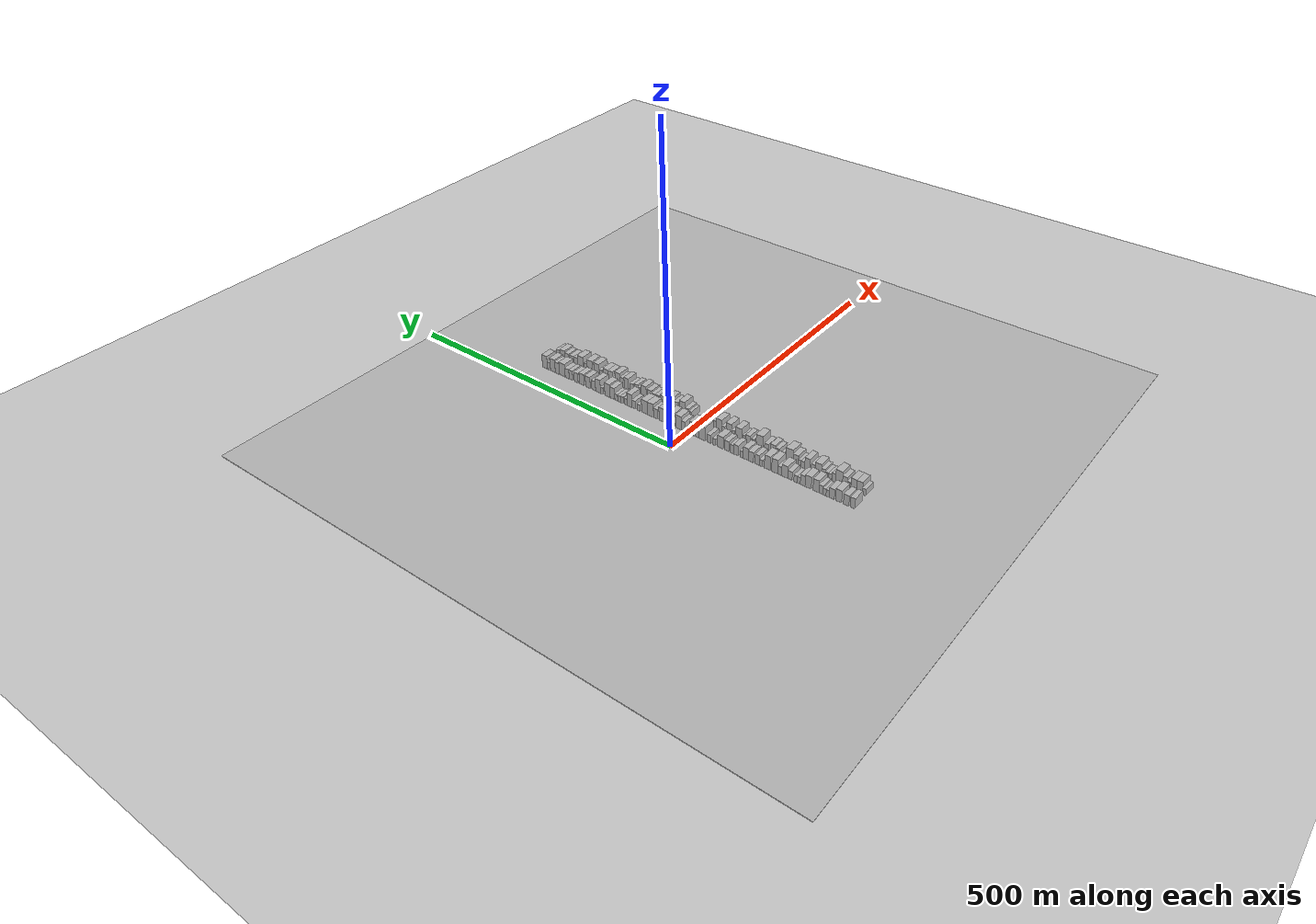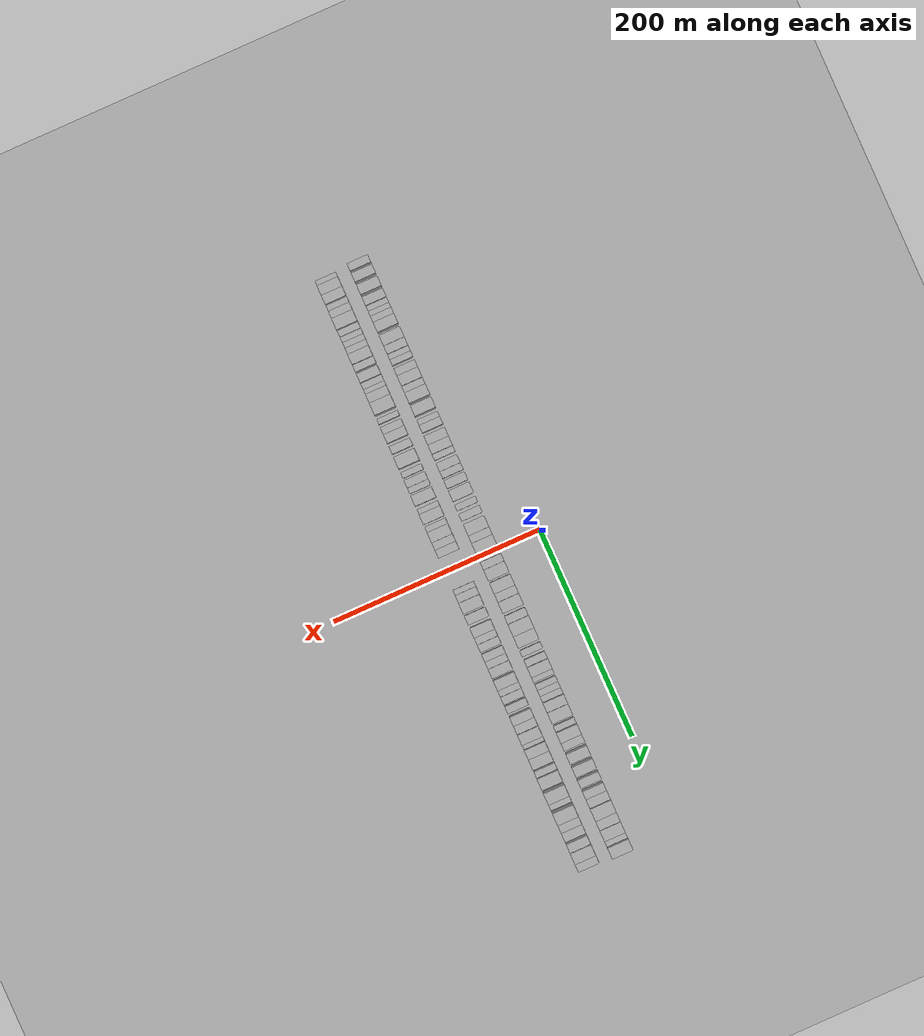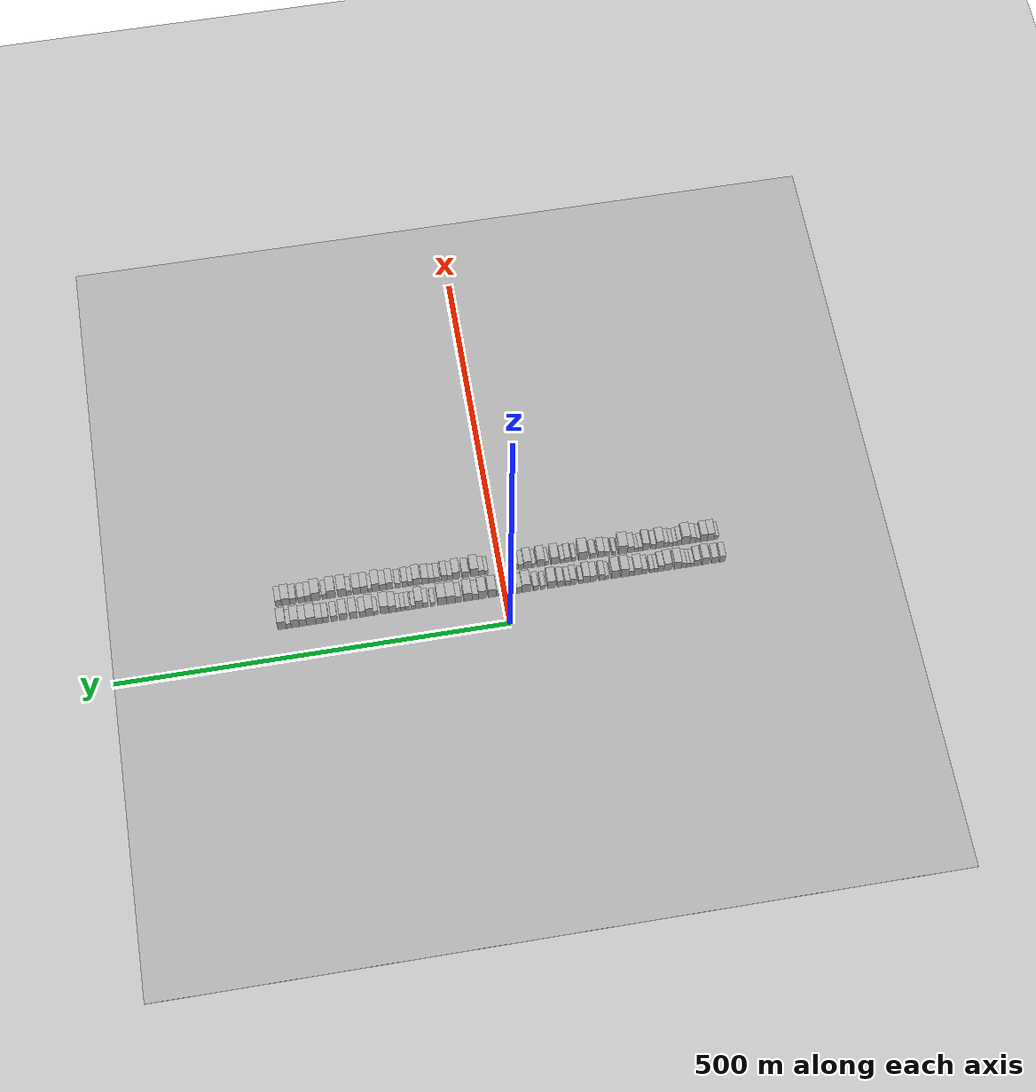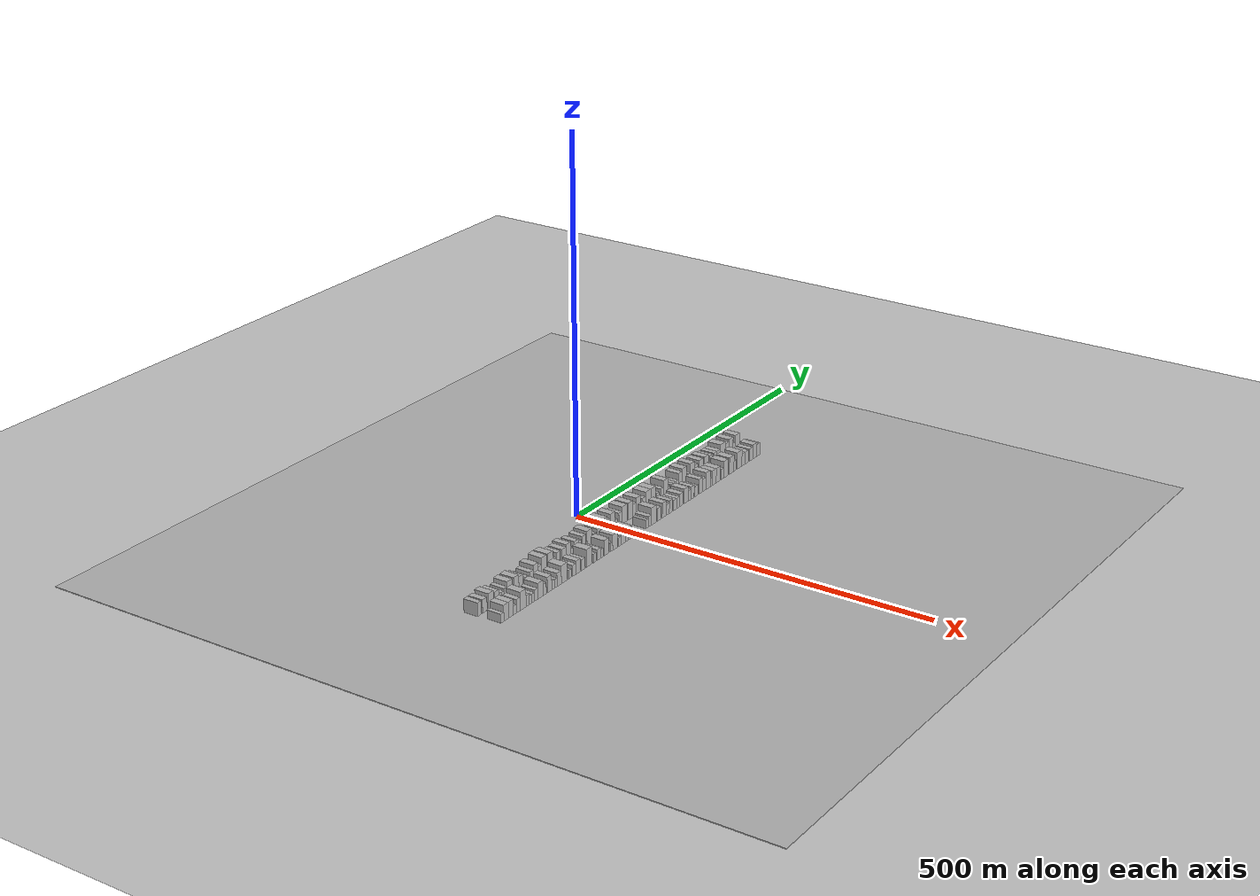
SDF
<?xml version="1.0" encoding="utf-8"?>

<sdf version="1.6">

   <world name="default">

      <gui fullscreen="0">

         <camera name="user_camera">

            <pose>-15 0 4.57585 0 0 0</pose>

            <view_controller>orbit</view_controller>

         </camera>

      </gui>

      <scene>

         <sky>

           <clouds>

             <speed>12</speed>

           </clouds>

         </sky>

         <ambient>0.4 0.4 0.4 1</ambient>

         <background>0.7 0.7 0.7 1</background>

         <shadows>1</shadows>

      </scene>

      <gravity>0 0 -9.8066</gravity>

      <magnetic_field>6e-06 2.3e-05 -4.2e-05</magnetic_field>

      <physics default="0" name="default_physics" type="ode">

         <ode>

            <solver>

               <type>quick</type>

               <iters>10</iters>

               <sor>1.0</sor>

               <use_dynamic_moi_rescaling>0</use_dynamic_moi_rescaling>

            </solver>

            <constraints>

               <cfm>0</cfm>

               <erp>0.2</erp>

               <contact_max_correcting_vel>100</contact_max_correcting_vel>

               <contact_surface_layer>0.001</contact_surface_layer>

            </constraints>

         </ode>

         <max_step_size>0.004</max_step_size>

         <real_time_factor>1</real_time_factor>

         <real_time_update_rate>250</real_time_update_rate>

      </physics>

      <light name="sun" type="directional">

         <cast_shadows>1</cast_shadows>

         <pose>0 0 10 0 0 0</pose>

         <diffuse>0.8 0.8 0.8 1</diffuse>

         <specular>0.2 0.2 0.2 1</specular>

         <attenuation>

            <range>1000</range>

            <constant>0.9</constant>

            <linear>0.01</linear>

            <quadratic>0.001</quadratic>

         </attenuation>

         <direction>-0.5 0.1 -0.9</direction>

      </light>

      <include>

         <name>ground_plane_1</name>

         <uri>model://HANNAS_ground_plane</uri>

         <pose>0 0 0  0 0 0</pose>

      </include>

      <include>

         <name>ground_plane_2</name>

         <uri>model://HANNAS_ground_plane</uri>

         <pose>100 0 0  0 0 0</pose>

      </include>

      <model name="building_1">

         <static>1</static>

         <pose frame="">50.0000 -280.3439 0 0.000000 0.000000 0.000000</pose>

         <link name="link">

            <pose frame="">0 0 9.00 0 0 0</pose>

            <collision name="collision">

               <geometry>

                  <box>

                     <size>20.0000 7.3122 18.0000</size>

                  </box>

               </geometry>

               <max_contacts>10</max_contacts>

               <surface>

                  <contact>

                     <ode/>

                  </contact>

                  <bounce/>

                  <friction>

                     <torsional>

                        <ode/>

                     </torsional>

                     <ode/>

                  </friction>

               </surface>

            </collision>

            <visual name="visual">

               <cast_shadows>0</cast_shadows>

               <geometry>

                  <box>

                     <size>20.0000 7.3122 18.0000</size>

                  </box>

               </geometry>

               <material>

                  <script>

                     <uri>model://HANNAS_wall/materials/scripts</uri>

                     <uri>model://HANNAS_wall/materials/textures</uri>

                     <name>vrc/HANNAS_wall</name>

                  </script>

               </material>

            </visual>

            <self_collide>0</self_collide>

            <enable_wind>0</enable_wind>

            <kinematic>0</kinematic>

         </link>

      </model>

      <model name="building_2">

         <static>1</static>

         <pose frame="">50.0000 -270.4074 0 0.000000 0.000000 0.000000</pose>

         <link name="link">

            <pose frame="">0 0 9.00 0 0 0</pose>

            <collision name="collision">

               <geometry>

                  <box>

                     <size>20.0000 8.5608 18.0000</size>

                  </box>

               </geometry>

               <max_contacts>10</max_contacts>

               <surface>

                  <contact>

                     <ode/>

                  </contact>

                  <bounce/>

                  <friction>

                     <torsional>

                        <ode/>

                     </torsional>

                     <ode/>

                  </friction>

               </surface>

            </collision>

            <visual name="visual">

               <cast_shadows>0</cast_shadows>

               <geometry>

                  <box>

                     <size>20.0000 8.5608 18.0000</size>

                  </box>

               </geometry>

               <material>

                  <script>

                     <uri>model://HANNAS_wall/materials/scripts</uri>

                     <uri>model://HANNAS_wall/materials/textures</uri>

                     <name>vrc/HANNAS_wall</name>

                  </script>

               </material>

            </visual>

            <self_collide>0</self_collide>

            <enable_wind>0</enable_wind>

            <kinematic>0</kinematic>

         </link>

      </model>

      <model name="building_3">

         <static>1</static>

         <pose frame="">50.0000 -258.3711 0 0.000000 0.000000 0.000000</pose>

         <link name="link">

            <pose frame="">0 0 10.50 0 0 0</pose>

            <collision name="collision">

               <geometry>

                  <box>

                     <size>20.0000 9.5118 21.0000</size>

                  </box>

               </geometry>

               <max_contacts>10</max_contacts>

               <surface>

                  <contact>

                     <ode/>

                  </contact>

                  <bounce/>

                  <friction>

                     <torsional>

                        <ode/>

                     </torsional>

                     <ode/>

                  </friction>

               </surface>

            </collision>

            <visual name="visual">

               <cast_shadows>0</cast_shadows>

               <geometry>

                  <box>

                     <size>20.0000 9.5118 21.0000</size>

                  </box>

               </geometry>

               <material>

                  <script>

                     <uri>model://HANNAS_wall/materials/scripts</uri>

                     <uri>model://HANNAS_wall/materials/textures</uri>

                     <name>vrc/HANNAS_wall</name>

                  </script>

               </material>

            </visual>

            <self_collide>0</self_collide>

            <enable_wind>0</enable_wind>

            <kinematic>0</kinematic>

         </link>

      </model>

      <model name="building_4">

         <static>1</static>

         <pose frame="">50.0000 -247.4853 0 0.000000 0.000000 0.000000</pose>

         <link name="link">

            <pose frame="">0 0 9.00 0 0 0</pose>

            <collision name="collision">

               <geometry>

                  <box>

                     <size>20.0000 8.2598 18.0000</size>

                  </box>

               </geometry>

               <max_contacts>10</max_contacts>

               <surface>

                  <contact>

                     <ode/>

                  </contact>

                  <bounce/>

                  <friction>

                     <torsional>

                        <ode/>

                     </torsional>

                     <ode/>

                  </friction>

               </surface>

            </collision>

            <visual name="visual">

               <cast_shadows>0</cast_shadows>

               <geometry>

                  <box>

                     <size>20.0000 8.2598 18.0000</size>

                  </box>

               </geometry>

               <material>

                  <script>

                     <uri>model://HANNAS_wall/materials/scripts</uri>

                     <uri>model://HANNAS_wall/materials/textures</uri>

                     <name>vrc/HANNAS_wall</name>

                  </script>

               </material>

            </visual>

            <self_collide>0</self_collide>

            <enable_wind>0</enable_wind>

            <kinematic>0</kinematic>

         </link>

      </model>

      <model name="building_5">

         <static>1</static>

         <pose frame="">50.0000 -240.8686 0 0.000000 0.000000 0.000000</pose>

         <link name="link">

            <pose frame="">0 0 6.00 0 0 0</pose>

            <collision name="collision">

               <geometry>

                  <box>

                     <size>20.0000 4.9736 12.0000</size>

                  </box>

               </geometry>

               <max_contacts>10</max_contacts>

               <surface>

                  <contact>

                     <ode/>

                  </contact>

                  <bounce/>

                  <friction>

                     <torsional>

                        <ode/>

                     </torsional>

                     <ode/>

                  </friction>

               </surface>

            </collision>

            <visual name="visual">

               <cast_shadows>0</cast_shadows>

               <geometry>

                  <box>

                     <size>20.0000 4.9736 12.0000</size>

                  </box>

               </geometry>

               <material>

                  <script>

                     <uri>model://HANNAS_wall/materials/scripts</uri>

                     <uri>model://HANNAS_wall/materials/textures</uri>

                     <name>vrc/HANNAS_wall</name>

                  </script>

               </material>

            </visual>

            <self_collide>0</self_collide>

            <enable_wind>0</enable_wind>

            <kinematic>0</kinematic>

         </link>

      </model>

      <model name="building_6">

         <static>1</static>

         <pose frame="">50.0000 -235.9490 0 0.000000 0.000000 0.000000</pose>

         <link name="link">

            <pose frame="">0 0 6.00 0 0 0</pose>

            <collision name="collision">

               <geometry>

                  <box>

                     <size>20.0000 4.8657 12.0000</size>

                  </box>

               </geometry>

               <max_contacts>10</max_contacts>

               <surface>

                  <contact>

                     <ode/>

                  </contact>

                  <bounce/>

                  <friction>

                     <torsional>

                        <ode/>

                     </torsional>

                     <ode/>

                  </friction>

               </surface>

            </collision>

            <visual name="visual">

               <cast_shadows>0</cast_shadows>

               <geometry>

                  <box>

                     <size>20.0000 4.8657 12.0000</size>

                  </box>

               </geometry>

               <material>

                  <script>

                     <uri>model://HANNAS_wall/materials/scripts</uri>

                     <uri>model://HANNAS_wall/materials/textures</uri>

                     <name>vrc/HANNAS_wall</name>

                  </script>

               </material>

            </visual>

            <self_collide>0</self_collide>

            <enable_wind>0</enable_wind>

            <kinematic>0</kinematic>

         </link>

      </model>

      <model name="building_7">

         <static>1</static>

         <pose frame="">50.0000 -230.2777 0 0.000000 0.000000 0.000000</pose>

         <link name="link">

            <pose frame="">0 0 7.50 0 0 0</pose>

            <collision name="collision">

               <geometry>

                  <box>

                     <size>20.0000 6.4767 15.0000</size>

                  </box>

               </geometry>

               <max_contacts>10</max_contacts>

               <surface>

                  <contact>

                     <ode/>

                  </contact>

                  <bounce/>

                  <friction>

                     <torsional>

                        <ode/>

                     </torsional>

                     <ode/>

                  </friction>

               </surface>

            </collision>

            <visual name="visual">

               <cast_shadows>0</cast_shadows>

               <geometry>

                  <box>

                     <size>20.0000 6.4767 15.0000</size>

                  </box>

               </geometry>

               <material>

                  <script>

                     <uri>model://HANNAS_wall/materials/scripts</uri>

                     <uri>model://HANNAS_wall/materials/textures</uri>

                     <name>vrc/HANNAS_wall</name>

                  </script>

               </material>

            </visual>

            <self_collide>0</self_collide>

            <enable_wind>0</enable_wind>

            <kinematic>0</kinematic>

         </link>

      </model>

      <model name="building_8">

         <static>1</static>

         <pose frame="">50.0000 -222.2050 0 0.000000 0.000000 0.000000</pose>

         <link name="link">

            <pose frame="">0 0 10.50 0 0 0</pose>

            <collision name="collision">

               <geometry>

                  <box>

                     <size>20.0000 9.6688 21.0000</size>

                  </box>

               </geometry>

               <max_contacts>10</max_contacts>

               <surface>

                  <contact>

                     <ode/>

                  </contact>

                  <bounce/>

                  <friction>

                     <torsional>

                        <ode/>

                     </torsional>

                     <ode/>

                  </friction>

               </surface>

            </collision>

            <visual name="visual">

               <cast_shadows>0</cast_shadows>

               <geometry>

                  <box>

                     <size>20.0000 9.6688 21.0000</size>

                  </box>

               </geometry>

               <material>

                  <script>

                     <uri>model://HANNAS_wall/materials/scripts</uri>

                     <uri>model://HANNAS_wall/materials/textures</uri>

                     <name>vrc/HANNAS_wall</name>

                  </script>

               </material>

            </visual>

            <self_collide>0</self_collide>

            <enable_wind>0</enable_wind>

            <kinematic>0</kinematic>

         </link>

      </model>

      <model name="building_9">

         <static>1</static>

         <pose frame="">50.0000 -209.3454 0 0.000000 0.000000 0.000000</pose>

         <link name="link">

            <pose frame="">0 0 10.50 0 0 0</pose>

            <collision name="collision">

               <geometry>

                  <box>

                     <size>20.0000 10.0503 21.0000</size>

                  </box>

               </geometry>

               <max_contacts>10</max_contacts>

               <surface>

                  <contact>

                     <ode/>

                  </contact>

                  <bounce/>

                  <friction>

                     <torsional>

                        <ode/>

                     </torsional>

                     <ode/>

                  </friction>

               </surface>

            </collision>

            <visual name="visual">

               <cast_shadows>0</cast_shadows>

               <geometry>

                  <box>

                     <size>20.0000 10.0503 21.0000</size>

                  </box>

               </geometry>

               <material>

                  <script>

                     <uri>model://HANNAS_wall/materials/scripts</uri>

                     <uri>model://HANNAS_wall/materials/textures</uri>

                     <name>vrc/HANNAS_wall</name>

                  </script>

               </material>

            </visual>

            <self_collide>0</self_collide>

            <enable_wind>0</enable_wind>

            <kinematic>0</kinematic>

         </link>

      </model>

      <model name="building_10">

         <static>1</static>

         <pose frame="">50.0000 -200.4345 0 0.000000 0.000000 0.000000</pose>

         <link name="link">

            <pose frame="">0 0 9.00 0 0 0</pose>

            <collision name="collision">

               <geometry>

                  <box>

                     <size>20.0000 7.7715 18.0000</size>

                  </box>

               </geometry>

               <max_contacts>10</max_contacts>

               <surface>

                  <contact>

                     <ode/>

                  </contact>

                  <bounce/>

                  <friction>

                     <torsional>

                        <ode/>

                     </torsional>

                     <ode/>

                  </friction>

               </surface>

            </collision>

            <visual name="visual">

               <cast_shadows>0</cast_shadows>

               <geometry>

                  <box>

                     <size>20.0000 7.7715 18.0000</size>

                  </box>

               </geometry>

               <material>

                  <script>

                     <uri>model://HANNAS_wall/materials/scripts</uri>

                     <uri>model://HANNAS_wall/materials/textures</uri>

                     <name>vrc/HANNAS_wall</name>

                  </script>

               </material>

            </visual>

            <self_collide>0</self_collide>

            <enable_wind>0</enable_wind>

            <kinematic>0</kinematic>

         </link>

      </model>

      <model name="building_11">

         <static>1</static>

         <pose frame="">50.0000 -194.0659 0 0.000000 0.000000 0.000000</pose>

         <link name="link">

            <pose frame="">0 0 6.00 0 0 0</pose>

            <collision name="collision">

               <geometry>

                  <box>

                     <size>20.0000 4.9657 12.0000</size>

                  </box>

               </geometry>

               <max_contacts>10</max_contacts>

               <surface>

                  <contact>

                     <ode/>

                  </contact>

                  <bounce/>

                  <friction>

                     <torsional>

                        <ode/>

                     </torsional>

                     <ode/>

                  </friction>

               </surface>

            </collision>

            <visual name="visual">

               <cast_shadows>0</cast_shadows>

               <geometry>

                  <box>

                     <size>20.0000 4.9657 12.0000</size>

                  </box>

               </geometry>

               <material>

                  <script>

                     <uri>model://HANNAS_wall/materials/scripts</uri>

                     <uri>model://HANNAS_wall/materials/textures</uri>

                     <name>vrc/HANNAS_wall</name>

                  </script>

               </material>

            </visual>

            <self_collide>0</self_collide>

            <enable_wind>0</enable_wind>

            <kinematic>0</kinematic>

         </link>

      </model>

      <model name="building_12">

         <static>1</static>

         <pose frame="">50.0000 -188.7464 0 0.000000 0.000000 0.000000</pose>

         <link name="link">

            <pose frame="">0 0 6.00 0 0 0</pose>

            <collision name="collision">

               <geometry>

                  <box>

                     <size>20.0000 5.6733 12.0000</size>

                  </box>

               </geometry>

               <max_contacts>10</max_contacts>

               <surface>

                  <contact>

                     <ode/>

                  </contact>

                  <bounce/>

                  <friction>

                     <torsional>

                        <ode/>

                     </torsional>

                     <ode/>

                  </friction>

               </surface>

            </collision>

            <visual name="visual">

               <cast_shadows>0</cast_shadows>

               <geometry>

                  <box>

                     <size>20.0000 5.6733 12.0000</size>

                  </box>

               </geometry>

               <material>

                  <script>

                     <uri>model://HANNAS_wall/materials/scripts</uri>

                     <uri>model://HANNAS_wall/materials/textures</uri>

                     <name>vrc/HANNAS_wall</name>

                  </script>

               </material>

            </visual>

            <self_collide>0</self_collide>

            <enable_wind>0</enable_wind>

            <kinematic>0</kinematic>

         </link>

      </model>

      <model name="building_13">

         <static>1</static>

         <pose frame="">50.0000 -179.1969 0 0.000000 0.000000 0.000000</pose>

         <link name="link">

            <pose frame="">0 0 7.50 0 0 0</pose>

            <collision name="collision">

               <geometry>

                  <box>

                     <size>20.0000 7.4257 15.0000</size>

                  </box>

               </geometry>

               <max_contacts>10</max_contacts>

               <surface>

                  <contact>

                     <ode/>

                  </contact>

                  <bounce/>

                  <friction>

                     <torsional>

                        <ode/>

                     </torsional>

                     <ode/>

                  </friction>

               </surface>

            </collision>

            <visual name="visual">

               <cast_shadows>0</cast_shadows>

               <geometry>

                  <box>

                     <size>20.0000 7.4257 15.0000</size>

                  </box>

               </geometry>

               <material>

                  <script>

                     <uri>model://HANNAS_wall/materials/scripts</uri>

                     <uri>model://HANNAS_wall/materials/textures</uri>

                     <name>vrc/HANNAS_wall</name>

                  </script>

               </material>

            </visual>

            <self_collide>0</self_collide>

            <enable_wind>0</enable_wind>

            <kinematic>0</kinematic>

         </link>

      </model>

      <model name="building_14">

         <static>1</static>

         <pose frame="">50.0000 -170.5419 0 0.000000 0.000000 0.000000</pose>

         <link name="link">

            <pose frame="">0 0 10.50 0 0 0</pose>

            <collision name="collision">

               <geometry>

                  <box>

                     <size>20.0000 9.8844 21.0000</size>

                  </box>

               </geometry>

               <max_contacts>10</max_contacts>

               <surface>

                  <contact>

                     <ode/>

                  </contact>

                  <bounce/>

                  <friction>

                     <torsional>

                        <ode/>

                     </torsional>

                     <ode/>

                  </friction>

               </surface>

            </collision>

            <visual name="visual">

               <cast_shadows>0</cast_shadows>

               <geometry>

                  <box>

                     <size>20.0000 9.8844 21.0000</size>

                  </box>

               </geometry>

               <material>

                  <script>

                     <uri>model://HANNAS_wall/materials/scripts</uri>

                     <uri>model://HANNAS_wall/materials/textures</uri>

                     <name>vrc/HANNAS_wall</name>

                  </script>

               </material>

            </visual>

            <self_collide>0</self_collide>

            <enable_wind>0</enable_wind>

            <kinematic>0</kinematic>

         </link>

      </model>

      <model name="building_15">

         <static>1</static>

         <pose frame="">50.0000 -162.2782 0 0.000000 0.000000 0.000000</pose>

         <link name="link">

            <pose frame="">0 0 7.50 0 0 0</pose>

            <collision name="collision">

               <geometry>

                  <box>

                     <size>20.0000 6.6430 15.0000</size>

                  </box>

               </geometry>

               <max_contacts>10</max_contacts>

               <surface>

                  <contact>

                     <ode/>

                  </contact>

                  <bounce/>

                  <friction>

                     <torsional>

                        <ode/>

                     </torsional>

                     <ode/>

                  </friction>

               </surface>

            </collision>

            <visual name="visual">

               <cast_shadows>0</cast_shadows>

               <geometry>

                  <box>

                     <size>20.0000 6.6430 15.0000</size>

                  </box>

               </geometry>

               <material>

                  <script>

                     <uri>model://HANNAS_wall/materials/scripts</uri>

                     <uri>model://HANNAS_wall/materials/textures</uri>

                     <name>vrc/HANNAS_wall</name>

                  </script>

               </material>

            </visual>

            <self_collide>0</self_collide>

            <enable_wind>0</enable_wind>

            <kinematic>0</kinematic>

         </link>

      </model>

      <model name="building_16">

         <static>1</static>

         <pose frame="">50.0000 -153.8165 0 0.000000 0.000000 0.000000</pose>

         <link name="link">

            <pose frame="">0 0 12.00 0 0 0</pose>

            <collision name="collision">

               <geometry>

                  <box>

                     <size>20.0000 10.2804 24.0000</size>

                  </box>

               </geometry>

               <max_contacts>10</max_contacts>

               <surface>

                  <contact>

                     <ode/>

                  </contact>

                  <bounce/>

                  <friction>

                     <torsional>

                        <ode/>

                     </torsional>

                     <ode/>

                  </friction>

               </surface>

            </collision>

            <visual name="visual">

               <cast_shadows>0</cast_shadows>

               <geometry>

                  <box>

                     <size>20.0000 10.2804 24.0000</size>

                  </box>

               </geometry>

               <material>

                  <script>

                     <uri>model://HANNAS_wall/materials/scripts</uri>

                     <uri>model://HANNAS_wall/materials/textures</uri>

                     <name>vrc/HANNAS_wall</name>

                  </script>

               </material>

            </visual>

            <self_collide>0</self_collide>

            <enable_wind>0</enable_wind>

            <kinematic>0</kinematic>

         </link>

      </model>

      <model name="building_17">

         <static>1</static>

         <pose frame="">50.0000 -141.4898 0 0.000000 0.000000 0.000000</pose>

         <link name="link">

            <pose frame="">0 0 12.00 0 0 0</pose>

            <collision name="collision">

               <geometry>

                  <box>

                     <size>20.0000 10.3730 24.0000</size>

                  </box>

               </geometry>

               <max_contacts>10</max_contacts>

               <surface>

                  <contact>

                     <ode/>

                  </contact>

                  <bounce/>

                  <friction>

                     <torsional>

                        <ode/>

                     </torsional>

                     <ode/>

                  </friction>

               </surface>

            </collision>

            <visual name="visual">

               <cast_shadows>0</cast_shadows>

               <geometry>

                  <box>

                     <size>20.0000 10.3730 24.0000</size>

                  </box>

               </geometry>

               <material>

                  <script>

                     <uri>model://HANNAS_wall/materials/scripts</uri>

                     <uri>model://HANNAS_wall/materials/textures</uri>

                     <name>vrc/HANNAS_wall</name>

                  </script>

               </material>

            </visual>

            <self_collide>0</self_collide>

            <enable_wind>0</enable_wind>

            <kinematic>0</kinematic>

         </link>

      </model>

      <model name="building_18">

         <static>1</static>

         <pose frame="">50.0000 -130.6135 0 0.000000 0.000000 0.000000</pose>

         <link name="link">

            <pose frame="">0 0 6.00 0 0 0</pose>

            <collision name="collision">

               <geometry>

                  <box>

                     <size>20.0000 5.3796 12.0000</size>

                  </box>

               </geometry>

               <max_contacts>10</max_contacts>

               <surface>

                  <contact>

                     <ode/>

                  </contact>

                  <bounce/>

                  <friction>

                     <torsional>

                        <ode/>

                     </torsional>

                     <ode/>

                  </friction>

               </surface>

            </collision>

            <visual name="visual">

               <cast_shadows>0</cast_shadows>

               <geometry>

                  <box>

                     <size>20.0000 5.3796 12.0000</size>

                  </box>

               </geometry>

               <material>

                  <script>

                     <uri>model://HANNAS_wall/materials/scripts</uri>

                     <uri>model://HANNAS_wall/materials/textures</uri>

                     <name>vrc/HANNAS_wall</name>

                  </script>

               </material>

            </visual>

            <self_collide>0</self_collide>

            <enable_wind>0</enable_wind>

            <kinematic>0</kinematic>

         </link>

      </model>

      <model name="building_19">

         <static>1</static>

         <pose frame="">50.0000 -124.2336 0 0.000000 0.000000 0.000000</pose>

         <link name="link">

            <pose frame="">0 0 9.00 0 0 0</pose>

            <collision name="collision">

               <geometry>

                  <box>

                     <size>20.0000 7.3801 18.0000</size>

                  </box>

               </geometry>

               <max_contacts>10</max_contacts>

               <surface>

                  <contact>

                     <ode/>

                  </contact>

                  <bounce/>

                  <friction>

                     <torsional>

                        <ode/>

                     </torsional>

                     <ode/>

                  </friction>

               </surface>

            </collision>

            <visual name="visual">

               <cast_shadows>0</cast_shadows>

               <geometry>

                  <box>

                     <size>20.0000 7.3801 18.0000</size>

                  </box>

               </geometry>

               <material>

                  <script>

                     <uri>model://HANNAS_wall/materials/scripts</uri>

                     <uri>model://HANNAS_wall/materials/textures</uri>

                     <name>vrc/HANNAS_wall</name>

                  </script>

               </material>

            </visual>

            <self_collide>0</self_collide>

            <enable_wind>0</enable_wind>

            <kinematic>0</kinematic>

         </link>

      </model>

      <model name="building_20">

         <static>1</static>

         <pose frame="">50.0000 -113.1429 0 0.000000 0.000000 0.000000</pose>

         <link name="link">

            <pose frame="">0 0 9.00 0 0 0</pose>

            <collision name="collision">

               <geometry>

                  <box>

                     <size>20.0000 8.8013 18.0000</size>

                  </box>

               </geometry>

               <max_contacts>10</max_contacts>

               <surface>

                  <contact>

                     <ode/>

                  </contact>

                  <bounce/>

                  <friction>

                     <torsional>

                        <ode/>

                     </torsional>

                     <ode/>

                  </friction>

               </surface>

            </collision>

            <visual name="visual">

               <cast_shadows>0</cast_shadows>

               <geometry>

                  <box>

                     <size>20.0000 8.8013 18.0000</size>

                  </box>

               </geometry>

               <material>

                  <script>

                     <uri>model://HANNAS_wall/materials/scripts</uri>

                     <uri>model://HANNAS_wall/materials/textures</uri>

                     <name>vrc/HANNAS_wall</name>

                  </script>

               </material>

            </visual>

            <self_collide>0</self_collide>

            <enable_wind>0</enable_wind>

            <kinematic>0</kinematic>

         </link>

      </model>

      <model name="building_21">

         <static>1</static>

         <pose frame="">50.0000 -104.2943 0 0.000000 0.000000 0.000000</pose>

         <link name="link">

            <pose frame="">0 0 10.50 0 0 0</pose>

            <collision name="collision">

               <geometry>

                  <box>

                     <size>20.0000 8.8958 21.0000</size>

                  </box>

               </geometry>

               <max_contacts>10</max_contacts>

               <surface>

                  <contact>

                     <ode/>

                  </contact>

                  <bounce/>

                  <friction>

                     <torsional>

                        <ode/>

                     </torsional>

                     <ode/>

                  </friction>

               </surface>

            </collision>

            <visual name="visual">

               <cast_shadows>0</cast_shadows>

               <geometry>

                  <box>

                     <size>20.0000 8.8958 21.0000</size>

                  </box>

               </geometry>

               <material>

                  <script>

                     <uri>model://HANNAS_wall/materials/scripts</uri>

                     <uri>model://HANNAS_wall/materials/textures</uri>

                     <name>vrc/HANNAS_wall</name>

                  </script>

               </material>

            </visual>

            <self_collide>0</self_collide>

            <enable_wind>0</enable_wind>

            <kinematic>0</kinematic>

         </link>

      </model>

      <model name="building_22">

         <static>1</static>

         <pose frame="">50.0000 -97.0274 0 0.000000 0.000000 0.000000</pose>

         <link name="link">

            <pose frame="">0 0 6.00 0 0 0</pose>

            <collision name="collision">

               <geometry>

                  <box>

                     <size>20.0000 5.6381 12.0000</size>

                  </box>

               </geometry>

               <max_contacts>10</max_contacts>

               <surface>

                  <contact>

                     <ode/>

                  </contact>

                  <bounce/>

                  <friction>

                     <torsional>

                        <ode/>

                     </torsional>

                     <ode/>

                  </friction>

               </surface>

            </collision>

            <visual name="visual">

               <cast_shadows>0</cast_shadows>

               <geometry>

                  <box>

                     <size>20.0000 5.6381 12.0000</size>

                  </box>

               </geometry>

               <material>

                  <script>

                     <uri>model://HANNAS_wall/materials/scripts</uri>

                     <uri>model://HANNAS_wall/materials/textures</uri>

                     <name>vrc/HANNAS_wall</name>

                  </script>

               </material>

            </visual>

            <self_collide>0</self_collide>

            <enable_wind>0</enable_wind>

            <kinematic>0</kinematic>

         </link>

      </model>

      <model name="building_23">

         <static>1</static>

         <pose frame="">50.0000 -87.2267 0 0.000000 0.000000 0.000000</pose>

         <link name="link">

            <pose frame="">0 0 9.00 0 0 0</pose>

            <collision name="collision">

               <geometry>

                  <box>

                     <size>20.0000 7.9634 18.0000</size>

                  </box>

               </geometry>

               <max_contacts>10</max_contacts>

               <surface>

                  <contact>

                     <ode/>

                  </contact>

                  <bounce/>

                  <friction>

                     <torsional>

                        <ode/>

                     </torsional>

                     <ode/>

                  </friction>

               </surface>

            </collision>

            <visual name="visual">

               <cast_shadows>0</cast_shadows>

               <geometry>

                  <box>

                     <size>20.0000 7.9634 18.0000</size>

                  </box>

               </geometry>

               <material>

                  <script>

                     <uri>model://HANNAS_wall/materials/scripts</uri>

                     <uri>model://HANNAS_wall/materials/textures</uri>

                     <name>vrc/HANNAS_wall</name>

                  </script>

               </material>

            </visual>

            <self_collide>0</self_collide>

            <enable_wind>0</enable_wind>

            <kinematic>0</kinematic>

         </link>

      </model>

      <model name="building_24">

         <static>1</static>

         <pose frame="">50.0000 -79.9753 0 0.000000 0.000000 0.000000</pose>

         <link name="link">

            <pose frame="">0 0 7.50 0 0 0</pose>

            <collision name="collision">

               <geometry>

                  <box>

                     <size>20.0000 6.5394 15.0000</size>

                  </box>

               </geometry>

               <max_contacts>10</max_contacts>

               <surface>

                  <contact>

                     <ode/>

                  </contact>

                  <bounce/>

                  <friction>

                     <torsional>

                        <ode/>

                     </torsional>

                     <ode/>

                  </friction>

               </surface>

            </collision>

            <visual name="visual">

               <cast_shadows>0</cast_shadows>

               <geometry>

                  <box>

                     <size>20.0000 6.5394 15.0000</size>

                  </box>

               </geometry>

               <material>

                  <script>

                     <uri>model://HANNAS_wall/materials/scripts</uri>

                     <uri>model://HANNAS_wall/materials/textures</uri>

                     <name>vrc/HANNAS_wall</name>

                  </script>

               </material>

            </visual>

            <self_collide>0</self_collide>

            <enable_wind>0</enable_wind>

            <kinematic>0</kinematic>

         </link>

      </model>

      <model name="building_25">

         <static>1</static>

         <pose frame="">50.0000 -70.7188 0 0.000000 0.000000 0.000000</pose>

         <link name="link">

            <pose frame="">0 0 9.00 0 0 0</pose>

            <collision name="collision">

               <geometry>

                  <box>

                     <size>20.0000 7.9738 18.0000</size>

                  </box>

               </geometry>

               <max_contacts>10</max_contacts>

               <surface>

                  <contact>

                     <ode/>

                  </contact>

                  <bounce/>

                  <friction>

                     <torsional>

                        <ode/>

                     </torsional>

                     <ode/>

                  </friction>

               </surface>

            </collision>

            <visual name="visual">

               <cast_shadows>0</cast_shadows>

               <geometry>

                  <box>

                     <size>20.0000 7.9738 18.0000</size>

                  </box>

               </geometry>

               <material>

                  <script>

                     <uri>model://HANNAS_wall/materials/scripts</uri>

                     <uri>model://HANNAS_wall/materials/textures</uri>

                     <name>vrc/HANNAS_wall</name>

                  </script>

               </material>

            </visual>

            <self_collide>0</self_collide>

            <enable_wind>0</enable_wind>

            <kinematic>0</kinematic>

         </link>

      </model>

      <model name="building_26">

         <static>1</static>

         <pose frame="">50.0000 -59.4857 0 0.000000 0.000000 0.000000</pose>

         <link name="link">

            <pose frame="">0 0 10.50 0 0 0</pose>

            <collision name="collision">

               <geometry>

                  <box>

                     <size>20.0000 10.4924 21.0000</size>

                  </box>

               </geometry>

               <max_contacts>10</max_contacts>

               <surface>

                  <contact>

                     <ode/>

                  </contact>

                  <bounce/>

                  <friction>

                     <torsional>

                        <ode/>

                     </torsional>

                     <ode/>

                  </friction>

               </surface>

            </collision>

            <visual name="visual">

               <cast_shadows>0</cast_shadows>

               <geometry>

                  <box>

                     <size>20.0000 10.4924 21.0000</size>

                  </box>

               </geometry>

               <material>

                  <script>

                     <uri>model://HANNAS_wall/materials/scripts</uri>

                     <uri>model://HANNAS_wall/materials/textures</uri>

                     <name>vrc/HANNAS_wall</name>

                  </script>

               </material>

            </visual>

            <self_collide>0</self_collide>

            <enable_wind>0</enable_wind>

            <kinematic>0</kinematic>

         </link>

      </model>

      <model name="building_27">

         <static>1</static>

         <pose frame="">50.0000 -48.3004 0 0.000000 0.000000 0.000000</pose>

         <link name="link">

            <pose frame="">0 0 6.00 0 0 0</pose>

            <collision name="collision">

               <geometry>

                  <box>

                     <size>20.0000 5.8781 12.0000</size>

                  </box>

               </geometry>

               <max_contacts>10</max_contacts>

               <surface>

                  <contact>

                     <ode/>

                  </contact>

                  <bounce/>

                  <friction>

                     <torsional>

                        <ode/>

                     </torsional>

                     <ode/>

                  </friction>

               </surface>

            </collision>

            <visual name="visual">

               <cast_shadows>0</cast_shadows>

               <geometry>

                  <box>

                     <size>20.0000 5.8781 12.0000</size>

                  </box>

               </geometry>

               <material>

                  <script>

                     <uri>model://HANNAS_wall/materials/scripts</uri>

                     <uri>model://HANNAS_wall/materials/textures</uri>

                     <name>vrc/HANNAS_wall</name>

                  </script>

               </material>

            </visual>

            <self_collide>0</self_collide>

            <enable_wind>0</enable_wind>

            <kinematic>0</kinematic>

         </link>

      </model>

      <model name="building_28">

         <static>1</static>

         <pose frame="">50.0000 -38.8582 0 0.000000 0.000000 0.000000</pose>

         <link name="link">

            <pose frame="">0 0 7.50 0 0 0</pose>

            <collision name="collision">

               <geometry>

                  <box>

                     <size>20.0000 7.0065 15.0000</size>

                  </box>

               </geometry>

               <max_contacts>10</max_contacts>

               <surface>

                  <contact>

                     <ode/>

                  </contact>

                  <bounce/>

                  <friction>

                     <torsional>

                        <ode/>

                     </torsional>

                     <ode/>

                  </friction>

               </surface>

            </collision>

            <visual name="visual">

               <cast_shadows>0</cast_shadows>

               <geometry>

                  <box>

                     <size>20.0000 7.0065 15.0000</size>

                  </box>

               </geometry>

               <material>

                  <script>

                     <uri>model://HANNAS_wall/materials/scripts</uri>

                     <uri>model://HANNAS_wall/materials/textures</uri>

                     <name>vrc/HANNAS_wall</name>

                  </script>

               </material>

            </visual>

            <self_collide>0</self_collide>

            <enable_wind>0</enable_wind>

            <kinematic>0</kinematic>

         </link>

      </model>

      <model name="building_29">

         <static>1</static>

         <pose frame="">50.0000 -26.8399 0 0.000000 0.000000 0.000000</pose>

         <link name="link">

            <pose frame="">0 0 12.00 0 0 0</pose>

            <collision name="collision">

               <geometry>

                  <box>

                     <size>20.0000 11.0300 24.0000</size>

                  </box>

               </geometry>

               <max_contacts>10</max_contacts>

               <surface>

                  <contact>

                     <ode/>

                  </contact>

                  <bounce/>

                  <friction>

                     <torsional>

                        <ode/>

                     </torsional>

                     <ode/>

                  </friction>

               </surface>

            </collision>

            <visual name="visual">

               <cast_shadows>0</cast_shadows>

               <geometry>

                  <box>

                     <size>20.0000 11.0300 24.0000</size>

                  </box>

               </geometry>

               <material>

                  <script>

                     <uri>model://HANNAS_wall/materials/scripts</uri>

                     <uri>model://HANNAS_wall/materials/textures</uri>

                     <name>vrc/HANNAS_wall</name>

                  </script>

               </material>

            </visual>

            <self_collide>0</self_collide>

            <enable_wind>0</enable_wind>

            <kinematic>0</kinematic>

         </link>

      </model>

      <model name="building_30">

         <static>1</static>

         <pose frame="">50.0000 -17.6912 0 0.000000 0.000000 0.000000</pose>

         <link name="link">

            <pose frame="">0 0 9.00 0 0 0</pose>

            <collision name="collision">

               <geometry>

                  <box>

                     <size>20.0000 7.2674 18.0000</size>

                  </box>

               </geometry>

               <max_contacts>10</max_contacts>

               <surface>

                  <contact>

                     <ode/>

                  </contact>

                  <bounce/>

                  <friction>

                     <torsional>

                        <ode/>

                     </torsional>

                     <ode/>

                  </friction>

               </surface>

            </collision>

            <visual name="visual">

               <cast_shadows>0</cast_shadows>

               <geometry>

                  <box>

                     <size>20.0000 7.2674 18.0000</size>

                  </box>

               </geometry>

               <material>

                  <script>

                     <uri>model://HANNAS_wall/materials/scripts</uri>

                     <uri>model://HANNAS_wall/materials/textures</uri>

                     <name>vrc/HANNAS_wall</name>

                  </script>

               </material>

            </visual>

            <self_collide>0</self_collide>

            <enable_wind>0</enable_wind>

            <kinematic>0</kinematic>

         </link>

      </model>

      <model name="building_31">

         <static>1</static>

         <pose frame="">50.0000 -8.8309 0 0.000000 0.000000 0.000000</pose>

         <link name="link">

            <pose frame="">0 0 12.00 0 0 0</pose>

            <collision name="collision">

               <geometry>

                  <box>

                     <size>20.0000 10.4532 24.0000</size>

                  </box>

               </geometry>

               <max_contacts>10</max_contacts>

               <surface>

                  <contact>

                     <ode/>

                  </contact>

                  <bounce/>

                  <friction>

                     <torsional>

                        <ode/>

                     </torsional>

                     <ode/>

                  </friction>

               </surface>

            </collision>

            <visual name="visual">

               <cast_shadows>0</cast_shadows>

               <geometry>

                  <box>

                     <size>20.0000 10.4532 24.0000</size>

                  </box>

               </geometry>

               <material>

                  <script>

                     <uri>model://HANNAS_wall/materials/scripts</uri>

                     <uri>model://HANNAS_wall/materials/textures</uri>

                     <name>vrc/HANNAS_wall</name>

                  </script>

               </material>

            </visual>

            <self_collide>0</self_collide>

            <enable_wind>0</enable_wind>

            <kinematic>0</kinematic>

         </link>

      </model>

      <model name="building_32">

         <static>1</static>

         <pose frame="">50.0000 -1.1557 0 0.000000 0.000000 0.000000</pose>

         <link name="link">

            <pose frame="">0 0 6.00 0 0 0</pose>

            <collision name="collision">

               <geometry>

                  <box>

                     <size>20.0000 4.8971 12.0000</size>

                  </box>

               </geometry>

               <max_contacts>10</max_contacts>

               <surface>

                  <contact>

                     <ode/>

                  </contact>

                  <bounce/>

                  <friction>

                     <torsional>

                        <ode/>

                     </torsional>

                     <ode/>

                  </friction>

               </surface>

            </collision>

            <visual name="visual">

               <cast_shadows>0</cast_shadows>

               <geometry>

                  <box>

                     <size>20.0000 4.8971 12.0000</size>

                  </box>

               </geometry>

               <material>

                  <script>

                     <uri>model://HANNAS_wall/materials/scripts</uri>

                     <uri>model://HANNAS_wall/materials/textures</uri>

                     <name>vrc/HANNAS_wall</name>

                  </script>

               </material>

            </visual>

            <self_collide>0</self_collide>

            <enable_wind>0</enable_wind>

            <kinematic>0</kinematic>

         </link>

      </model>

      <model name="building_33">

         <static>1</static>

         <pose frame="">50.0000 7.9484 0 0.000000 0.000000 0.000000</pose>

         <link name="link">

            <pose frame="">0 0 9.00 0 0 0</pose>

            <collision name="collision">

               <geometry>

                  <box>

                     <size>20.0000 7.3112 18.0000</size>

                  </box>

               </geometry>

               <max_contacts>10</max_contacts>

               <surface>

                  <contact>

                     <ode/>

                  </contact>

                  <bounce/>

                  <friction>

                     <torsional>

                        <ode/>

                     </torsional>

                     <ode/>

                  </friction>

               </surface>

            </collision>

            <visual name="visual">

               <cast_shadows>0</cast_shadows>

               <geometry>

                  <box>

                     <size>20.0000 7.3112 18.0000</size>

                  </box>

               </geometry>

               <material>

                  <script>

                     <uri>model://HANNAS_wall/materials/scripts</uri>

                     <uri>model://HANNAS_wall/materials/textures</uri>

                     <name>vrc/HANNAS_wall</name>

                  </script>

               </material>

            </visual>

            <self_collide>0</self_collide>

            <enable_wind>0</enable_wind>

            <kinematic>0</kinematic>

         </link>

      </model>

      <model name="building_34">

         <static>1</static>

         <pose frame="">50.0000 16.9295 0 0.000000 0.000000 0.000000</pose>

         <link name="link">

            <pose frame="">0 0 12.00 0 0 0</pose>

            <collision name="collision">

               <geometry>

                  <box>

                     <size>20.0000 10.6510 24.0000</size>

                  </box>

               </geometry>

               <max_contacts>10</max_contacts>

               <surface>

                  <contact>

                     <ode/>

                  </contact>

                  <bounce/>

                  <friction>

                     <torsional>

                        <ode/>

                     </torsional>

                     <ode/>

                  </friction>

               </surface>

            </collision>

            <visual name="visual">

               <cast_shadows>0</cast_shadows>

               <geometry>

                  <box>

                     <size>20.0000 10.6510 24.0000</size>

                  </box>

               </geometry>

               <material>

                  <script>

                     <uri>model://HANNAS_wall/materials/scripts</uri>

                     <uri>model://HANNAS_wall/materials/textures</uri>

                     <name>vrc/HANNAS_wall</name>

                  </script>

               </material>

            </visual>

            <self_collide>0</self_collide>

            <enable_wind>0</enable_wind>

            <kinematic>0</kinematic>

         </link>

      </model>

      <model name="building_35">

         <static>1</static>

         <pose frame="">50.0000 29.4713 0 0.000000 0.000000 0.000000</pose>

         <link name="link">

            <pose frame="">0 0 12.00 0 0 0</pose>

            <collision name="collision">

               <geometry>

                  <box>

                     <size>20.0000 10.4326 24.0000</size>

                  </box>

               </geometry>

               <max_contacts>10</max_contacts>

               <surface>

                  <contact>

                     <ode/>

                  </contact>

                  <bounce/>

                  <friction>

                     <torsional>

                        <ode/>

                     </torsional>

                     <ode/>

                  </friction>

               </surface>

            </collision>

            <visual name="visual">

               <cast_shadows>0</cast_shadows>

               <geometry>

                  <box>

                     <size>20.0000 10.4326 24.0000</size>

                  </box>

               </geometry>

               <material>

                  <script>

                     <uri>model://HANNAS_wall/materials/scripts</uri>

                     <uri>model://HANNAS_wall/materials/textures</uri>

                     <name>vrc/HANNAS_wall</name>

                  </script>

               </material>

            </visual>

            <self_collide>0</self_collide>

            <enable_wind>0</enable_wind>

            <kinematic>0</kinematic>

         </link>

      </model>

      <model name="building_36">

         <static>1</static>

         <pose frame="">50.0000 38.7180 0 0.000000 0.000000 0.000000</pose>

         <link name="link">

            <pose frame="">0 0 9.00 0 0 0</pose>

            <collision name="collision">

               <geometry>

                  <box>

                     <size>20.0000 8.0610 18.0000</size>

                  </box>

               </geometry>

               <max_contacts>10</max_contacts>

               <surface>

                  <contact>

                     <ode/>

                  </contact>

                  <bounce/>

                  <friction>

                     <torsional>

                        <ode/>

                     </torsional>

                     <ode/>

                  </friction>

               </surface>

            </collision>

            <visual name="visual">

               <cast_shadows>0</cast_shadows>

               <geometry>

                  <box>

                     <size>20.0000 8.0610 18.0000</size>

                  </box>

               </geometry>

               <material>

                  <script>

                     <uri>model://HANNAS_wall/materials/scripts</uri>

                     <uri>model://HANNAS_wall/materials/textures</uri>

                     <name>vrc/HANNAS_wall</name>

                  </script>

               </material>

            </visual>

            <self_collide>0</self_collide>

            <enable_wind>0</enable_wind>

            <kinematic>0</kinematic>

         </link>

      </model>

      <model name="building_37">

         <static>1</static>

         <pose frame="">50.0000 48.0742 0 0.000000 0.000000 0.000000</pose>

         <link name="link">

            <pose frame="">0 0 12.00 0 0 0</pose>

            <collision name="collision">

               <geometry>

                  <box>

                     <size>20.0000 10.6514 24.0000</size>

                  </box>

               </geometry>

               <max_contacts>10</max_contacts>

               <surface>

                  <contact>

                     <ode/>

                  </contact>

                  <bounce/>

                  <friction>

                     <torsional>

                        <ode/>

                     </torsional>

                     <ode/>

                  </friction>

               </surface>

            </collision>

            <visual name="visual">

               <cast_shadows>0</cast_shadows>

               <geometry>

                  <box>

                     <size>20.0000 10.6514 24.0000</size>

                  </box>

               </geometry>

               <material>

                  <script>

                     <uri>model://HANNAS_wall/materials/scripts</uri>

                     <uri>model://HANNAS_wall/materials/textures</uri>

                     <name>vrc/HANNAS_wall</name>

                  </script>

               </material>

            </visual>

            <self_collide>0</self_collide>

            <enable_wind>0</enable_wind>

            <kinematic>0</kinematic>

         </link>

      </model>

      <model name="building_38">

         <static>1</static>

         <pose frame="">50.0000 60.2064 0 0.000000 0.000000 0.000000</pose>

         <link name="link">

            <pose frame="">0 0 9.00 0 0 0</pose>

            <collision name="collision">

               <geometry>

                  <box>

                     <size>20.0000 7.6129 18.0000</size>

                  </box>

               </geometry>

               <max_contacts>10</max_contacts>

               <surface>

                  <contact>

                     <ode/>

                  </contact>

                  <bounce/>

                  <friction>

                     <torsional>

                        <ode/>

                     </torsional>

                     <ode/>

                  </friction>

               </surface>

            </collision>

            <visual name="visual">

               <cast_shadows>0</cast_shadows>

               <geometry>

                  <box>

                     <size>20.0000 7.6129 18.0000</size>

                  </box>

               </geometry>

               <material>

                  <script>

                     <uri>model://HANNAS_wall/materials/scripts</uri>

                     <uri>model://HANNAS_wall/materials/textures</uri>

                     <name>vrc/HANNAS_wall</name>

                  </script>

               </material>

            </visual>

            <self_collide>0</self_collide>

            <enable_wind>0</enable_wind>

            <kinematic>0</kinematic>

         </link>

      </model>

      <model name="building_39">

         <static>1</static>

         <pose frame="">50.0000 69.8949 0 0.000000 0.000000 0.000000</pose>

         <link name="link">

            <pose frame="">0 0 12.00 0 0 0</pose>

            <collision name="collision">

               <geometry>

                  <box>

                     <size>20.0000 11.7640 24.0000</size>

                  </box>

               </geometry>

               <max_contacts>10</max_contacts>

               <surface>

                  <contact>

                     <ode/>

                  </contact>

                  <bounce/>

                  <friction>

                     <torsional>

                        <ode/>

                     </torsional>

                     <ode/>

                  </friction>

               </surface>

            </collision>

            <visual name="visual">

               <cast_shadows>0</cast_shadows>

               <geometry>

                  <box>

                     <size>20.0000 11.7640 24.0000</size>

                  </box>

               </geometry>

               <material>

                  <script>

                     <uri>model://HANNAS_wall/materials/scripts</uri>

                     <uri>model://HANNAS_wall/materials/textures</uri>

                     <name>vrc/HANNAS_wall</name>

                  </script>

               </material>

            </visual>

            <self_collide>0</self_collide>

            <enable_wind>0</enable_wind>

            <kinematic>0</kinematic>

         </link>

      </model>

      <model name="building_40">

         <static>1</static>

         <pose frame="">50.0000 81.3257 0 0.000000 0.000000 0.000000</pose>

         <link name="link">

            <pose frame="">0 0 12.00 0 0 0</pose>

            <collision name="collision">

               <geometry>

                  <box>

                     <size>20.0000 11.0977 24.0000</size>

                  </box>

               </geometry>

               <max_contacts>10</max_contacts>

               <surface>

                  <contact>

                     <ode/>

                  </contact>

                  <bounce/>

                  <friction>

                     <torsional>

                        <ode/>

                     </torsional>

                     <ode/>

                  </friction>

               </surface>

            </collision>

            <visual name="visual">

               <cast_shadows>0</cast_shadows>

               <geometry>

                  <box>

                     <size>20.0000 11.0977 24.0000</size>

                  </box>

               </geometry>

               <material>

                  <script>

                     <uri>model://HANNAS_wall/materials/scripts</uri>

                     <uri>model://HANNAS_wall/materials/textures</uri>

                     <name>vrc/HANNAS_wall</name>

                  </script>

               </material>

            </visual>

            <self_collide>0</self_collide>

            <enable_wind>0</enable_wind>

            <kinematic>0</kinematic>

         </link>

      </model>

      <model name="building_41">

         <static>1</static>

         <pose frame="">50.0000 92.8498 0 0.000000 0.000000 0.000000</pose>

         <link name="link">

            <pose frame="">0 0 6.00 0 0 0</pose>

            <collision name="collision">

               <geometry>

                  <box>

                     <size>20.0000 5.9505 12.0000</size>

                  </box>

               </geometry>

               <max_contacts>10</max_contacts>

               <surface>

                  <contact>

                     <ode/>

                  </contact>

                  <bounce/>

                  <friction>

                     <torsional>

                        <ode/>

                     </torsional>

                     <ode/>

                  </friction>

               </surface>

            </collision>

            <visual name="visual">

               <cast_shadows>0</cast_shadows>

               <geometry>

                  <box>

                     <size>20.0000 5.9505 12.0000</size>

                  </box>

               </geometry>

               <material>

                  <script>

                     <uri>model://HANNAS_wall/materials/scripts</uri>

                     <uri>model://HANNAS_wall/materials/textures</uri>

                     <name>vrc/HANNAS_wall</name>

                  </script>

               </material>

            </visual>

            <self_collide>0</self_collide>

            <enable_wind>0</enable_wind>

            <kinematic>0</kinematic>

         </link>

      </model>

      <model name="building_42">

         <static>1</static>

         <pose frame="">50.0000 102.1915 0 0.000000 0.000000 0.000000</pose>

         <link name="link">

            <pose frame="">0 0 7.50 0 0 0</pose>

            <collision name="collision">

               <geometry>

                  <box>

                     <size>20.0000 6.7328 15.0000</size>

                  </box>

               </geometry>

               <max_contacts>10</max_contacts>

               <surface>

                  <contact>

                     <ode/>

                  </contact>

                  <bounce/>

                  <friction>

                     <torsional>

                        <ode/>

                     </torsional>

                     <ode/>

                  </friction>

               </surface>

            </collision>

            <visual name="visual">

               <cast_shadows>0</cast_shadows>

               <geometry>

                  <box>

                     <size>20.0000 6.7328 15.0000</size>

                  </box>

               </geometry>

               <material>

                  <script>

                     <uri>model://HANNAS_wall/materials/scripts</uri>

                     <uri>model://HANNAS_wall/materials/textures</uri>

                     <name>vrc/HANNAS_wall</name>

                  </script>

               </material>

            </visual>

            <self_collide>0</self_collide>

            <enable_wind>0</enable_wind>

            <kinematic>0</kinematic>

         </link>

      </model>

      <model name="building_43">

         <static>1</static>

         <pose frame="">50.0000 110.3665 0 0.000000 0.000000 0.000000</pose>

         <link name="link">

            <pose frame="">0 0 12.00 0 0 0</pose>

            <collision name="collision">

               <geometry>

                  <box>

                     <size>20.0000 9.6173 24.0000</size>

                  </box>

               </geometry>

               <max_contacts>10</max_contacts>

               <surface>

                  <contact>

                     <ode/>

                  </contact>

                  <bounce/>

                  <friction>

                     <torsional>

                        <ode/>

                     </torsional>

                     <ode/>

                  </friction>

               </surface>

            </collision>

            <visual name="visual">

               <cast_shadows>0</cast_shadows>

               <geometry>

                  <box>

                     <size>20.0000 9.6173 24.0000</size>

                  </box>

               </geometry>

               <material>

                  <script>

                     <uri>model://HANNAS_wall/materials/scripts</uri>

                     <uri>model://HANNAS_wall/materials/textures</uri>

                     <name>vrc/HANNAS_wall</name>

                  </script>

               </material>

            </visual>

            <self_collide>0</self_collide>

            <enable_wind>0</enable_wind>

            <kinematic>0</kinematic>

         </link>

      </model>

      <model name="building_44">

         <static>1</static>

         <pose frame="">50.0000 117.9089 0 0.000000 0.000000 0.000000</pose>

         <link name="link">

            <pose frame="">0 0 6.00 0 0 0</pose>

            <collision name="collision">

               <geometry>

                  <box>

                     <size>20.0000 5.4675 12.0000</size>

                  </box>

               </geometry>

               <max_contacts>10</max_contacts>

               <surface>

                  <contact>

                     <ode/>

                  </contact>

                  <bounce/>

                  <friction>

                     <torsional>

                        <ode/>

                     </torsional>

                     <ode/>

                  </friction>

               </surface>

            </collision>

            <visual name="visual">

               <cast_shadows>0</cast_shadows>

               <geometry>

                  <box>

                     <size>20.0000 5.4675 12.0000</size>

                  </box>

               </geometry>

               <material>

                  <script>

                     <uri>model://HANNAS_wall/materials/scripts</uri>

                     <uri>model://HANNAS_wall/materials/textures</uri>

                     <name>vrc/HANNAS_wall</name>

                  </script>

               </material>

            </visual>

            <self_collide>0</self_collide>

            <enable_wind>0</enable_wind>

            <kinematic>0</kinematic>

         </link>

      </model>

      <model name="building_45">

         <static>1</static>

         <pose frame="">50.0000 125.4124 0 0.000000 0.000000 0.000000</pose>

         <link name="link">

            <pose frame="">0 0 6.00 0 0 0</pose>

            <collision name="collision">

               <geometry>

                  <box>

                     <size>20.0000 5.5394 12.0000</size>

                  </box>

               </geometry>

               <max_contacts>10</max_contacts>

               <surface>

                  <contact>

                     <ode/>

                  </contact>

                  <bounce/>

                  <friction>

                     <torsional>

                        <ode/>

                     </torsional>

                     <ode/>

                  </friction>

               </surface>

            </collision>

            <visual name="visual">

               <cast_shadows>0</cast_shadows>

               <geometry>

                  <box>

                     <size>20.0000 5.5394 12.0000</size>

                  </box>

               </geometry>

               <material>

                  <script>

                     <uri>model://HANNAS_wall/materials/scripts</uri>

                     <uri>model://HANNAS_wall/materials/textures</uri>

                     <name>vrc/HANNAS_wall</name>

                  </script>

               </material>

            </visual>

            <self_collide>0</self_collide>

            <enable_wind>0</enable_wind>

            <kinematic>0</kinematic>

         </link>

      </model>

      <model name="building_46">

         <static>1</static>

         <pose frame="">50.0000 131.1066 0 0.000000 0.000000 0.000000</pose>

         <link name="link">

            <pose frame="">0 0 6.00 0 0 0</pose>

            <collision name="collision">

               <geometry>

                  <box>

                     <size>20.0000 5.8488 12.0000</size>

                  </box>

               </geometry>

               <max_contacts>10</max_contacts>

               <surface>

                  <contact>

                     <ode/>

                  </contact>

                  <bounce/>

                  <friction>

                     <torsional>

                        <ode/>

                     </torsional>

                     <ode/>

                  </friction>

               </surface>

            </collision>

            <visual name="visual">

               <cast_shadows>0</cast_shadows>

               <geometry>

                  <box>

                     <size>20.0000 5.8488 12.0000</size>

                  </box>

               </geometry>

               <material>

                  <script>

                     <uri>model://HANNAS_wall/materials/scripts</uri>

                     <uri>model://HANNAS_wall/materials/textures</uri>

                     <name>vrc/HANNAS_wall</name>

                  </script>

               </material>

            </visual>

            <self_collide>0</self_collide>

            <enable_wind>0</enable_wind>

            <kinematic>0</kinematic>

         </link>

      </model>

      <model name="building_47">

         <static>1</static>

         <pose frame="">50.0000 136.9455 0 0.000000 0.000000 0.000000</pose>

         <link name="link">

            <pose frame="">0 0 6.00 0 0 0</pose>

            <collision name="collision">

               <geometry>

                  <box>

                     <size>20.0000 5.8291 12.0000</size>

                  </box>

               </geometry>

               <max_contacts>10</max_contacts>

               <surface>

                  <contact>

                     <ode/>

                  </contact>

                  <bounce/>

                  <friction>

                     <torsional>

                        <ode/>

                     </torsional>

                     <ode/>

                  </friction>

               </surface>

            </collision>

            <visual name="visual">

               <cast_shadows>0</cast_shadows>

               <geometry>

                  <box>

                     <size>20.0000 5.8291 12.0000</size>

                  </box>

               </geometry>

               <material>

                  <script>

                     <uri>model://HANNAS_wall/materials/scripts</uri>

                     <uri>model://HANNAS_wall/materials/textures</uri>

                     <name>vrc/HANNAS_wall</name>

                  </script>

               </material>

            </visual>

            <self_collide>0</self_collide>

            <enable_wind>0</enable_wind>

            <kinematic>0</kinematic>

         </link>

      </model>

      <model name="building_48">

         <static>1</static>

         <pose frame="">50.0000 144.4742 0 0.000000 0.000000 0.000000</pose>

         <link name="link">

            <pose frame="">0 0 10.50 0 0 0</pose>

            <collision name="collision">

               <geometry>

                  <box>

                     <size>20.0000 9.2283 21.0000</size>

                  </box>

               </geometry>

               <max_contacts>10</max_contacts>

               <surface>

                  <contact>

                     <ode/>

                  </contact>

                  <bounce/>

                  <friction>

                     <torsional>

                        <ode/>

                     </torsional>

                     <ode/>

                  </friction>

               </surface>

            </collision>

            <visual name="visual">

               <cast_shadows>0</cast_shadows>

               <geometry>

                  <box>

                     <size>20.0000 9.2283 21.0000</size>

                  </box>

               </geometry>

               <material>

                  <script>

                     <uri>model://HANNAS_wall/materials/scripts</uri>

                     <uri>model://HANNAS_wall/materials/textures</uri>

                     <name>vrc/HANNAS_wall</name>

                  </script>

               </material>

            </visual>

            <self_collide>0</self_collide>

            <enable_wind>0</enable_wind>

            <kinematic>0</kinematic>

         </link>

      </model>

      <model name="building_49">

         <static>1</static>

         <pose frame="">50.0000 154.4830 0 0.000000 0.000000 0.000000</pose>

         <link name="link">

            <pose frame="">0 0 12.00 0 0 0</pose>

            <collision name="collision">

               <geometry>

                  <box>

                     <size>20.0000 10.7894 24.0000</size>

                  </box>

               </geometry>

               <max_contacts>10</max_contacts>

               <surface>

                  <contact>

                     <ode/>

                  </contact>

                  <bounce/>

                  <friction>

                     <torsional>

                        <ode/>

                     </torsional>

                     <ode/>

                  </friction>

               </surface>

            </collision>

            <visual name="visual">

               <cast_shadows>0</cast_shadows>

               <geometry>

                  <box>

                     <size>20.0000 10.7894 24.0000</size>

                  </box>

               </geometry>

               <material>

                  <script>

                     <uri>model://HANNAS_wall/materials/scripts</uri>

                     <uri>model://HANNAS_wall/materials/textures</uri>

                     <name>vrc/HANNAS_wall</name>

                  </script>

               </material>

            </visual>

            <self_collide>0</self_collide>

            <enable_wind>0</enable_wind>

            <kinematic>0</kinematic>

         </link>

      </model>

      <model name="building_50">

         <static>1</static>

         <pose frame="">50.0000 165.6741 0 0.000000 0.000000 0.000000</pose>

         <link name="link">

            <pose frame="">0 0 6.00 0 0 0</pose>

            <collision name="collision">

               <geometry>

                  <box>

                     <size>20.0000 5.5927 12.0000</size>

                  </box>

               </geometry>

               <max_contacts>10</max_contacts>

               <surface>

                  <contact>

                     <ode/>

                  </contact>

                  <bounce/>

                  <friction>

                     <torsional>

                        <ode/>

                     </torsional>

                     <ode/>

                  </friction>

               </surface>

            </collision>

            <visual name="visual">

               <cast_shadows>0</cast_shadows>

               <geometry>

                  <box>

                     <size>20.0000 5.5927 12.0000</size>

                  </box>

               </geometry>

               <material>

                  <script>

                     <uri>model://HANNAS_wall/materials/scripts</uri>

                     <uri>model://HANNAS_wall/materials/textures</uri>

                     <name>vrc/HANNAS_wall</name>

                  </script>

               </material>

            </visual>

            <self_collide>0</self_collide>

            <enable_wind>0</enable_wind>

            <kinematic>0</kinematic>

         </link>

      </model>

      <model name="building_51">

         <static>1</static>

         <pose frame="">50.0000 173.4579 0 0.000000 0.000000 0.000000</pose>

         <link name="link">

            <pose frame="">0 0 12.00 0 0 0</pose>

            <collision name="collision">

               <geometry>

                  <box>

                     <size>20.0000 9.9750 24.0000</size>

                  </box>

               </geometry>

               <max_contacts>10</max_contacts>

               <surface>

                  <contact>

                     <ode/>

                  </contact>

                  <bounce/>

                  <friction>

                     <torsional>

                        <ode/>

                     </torsional>

                     <ode/>

                  </friction>

               </surface>

            </collision>

            <visual name="visual">

               <cast_shadows>0</cast_shadows>

               <geometry>

                  <box>

                     <size>20.0000 9.9750 24.0000</size>

                  </box>

               </geometry>

               <material>

                  <script>

                     <uri>model://HANNAS_wall/materials/scripts</uri>

                     <uri>model://HANNAS_wall/materials/textures</uri>

                     <name>vrc/HANNAS_wall</name>

                  </script>

               </material>

            </visual>

            <self_collide>0</self_collide>

            <enable_wind>0</enable_wind>

            <kinematic>0</kinematic>

         </link>

      </model>

      <model name="building_52">

         <static>1</static>

         <pose frame="">50.0000 182.3927 0 0.000000 0.000000 0.000000</pose>

         <link name="link">

            <pose frame="">0 0 9.00 0 0 0</pose>

            <collision name="collision">

               <geometry>

                  <box>

                     <size>20.0000 7.8946 18.0000</size>

                  </box>

               </geometry>

               <max_contacts>10</max_contacts>

               <surface>

                  <contact>

                     <ode/>

                  </contact>

                  <bounce/>

                  <friction>

                     <torsional>

                        <ode/>

                     </torsional>

                     <ode/>

                  </friction>

               </surface>

            </collision>

            <visual name="visual">

               <cast_shadows>0</cast_shadows>

               <geometry>

                  <box>

                     <size>20.0000 7.8946 18.0000</size>

                  </box>

               </geometry>

               <material>

                  <script>

                     <uri>model://HANNAS_wall/materials/scripts</uri>

                     <uri>model://HANNAS_wall/materials/textures</uri>

                     <name>vrc/HANNAS_wall</name>

                  </script>

               </material>

            </visual>

            <self_collide>0</self_collide>

            <enable_wind>0</enable_wind>

            <kinematic>0</kinematic>

         </link>

      </model>

      <model name="building_53">

         <static>1</static>

         <pose frame="">50.0000 194.1213 0 0.000000 0.000000 0.000000</pose>

         <link name="link">

            <pose frame="">0 0 10.50 0 0 0</pose>

            <collision name="collision">

               <geometry>

                  <box>

                     <size>20.0000 9.5626 21.0000</size>

                  </box>

               </geometry>

               <max_contacts>10</max_contacts>

               <surface>

                  <contact>

                     <ode/>

                  </contact>

                  <bounce/>

                  <friction>

                     <torsional>

                        <ode/>

                     </torsional>

                     <ode/>

                  </friction>

               </surface>

            </collision>

            <visual name="visual">

               <cast_shadows>0</cast_shadows>

               <geometry>

                  <box>

                     <size>20.0000 9.5626 21.0000</size>

                  </box>

               </geometry>

               <material>

                  <script>

                     <uri>model://HANNAS_wall/materials/scripts</uri>

                     <uri>model://HANNAS_wall/materials/textures</uri>

                     <name>vrc/HANNAS_wall</name>

                  </script>

               </material>

            </visual>

            <self_collide>0</self_collide>

            <enable_wind>0</enable_wind>

            <kinematic>0</kinematic>

         </link>

      </model>

      <model name="building_54">

         <static>1</static>

         <pose frame="">50.0000 206.7688 0 0.000000 0.000000 0.000000</pose>

         <link name="link">

            <pose frame="">0 0 10.50 0 0 0</pose>

            <collision name="collision">

               <geometry>

                  <box>

                     <size>20.0000 9.7323 21.0000</size>

                  </box>

               </geometry>

               <max_contacts>10</max_contacts>

               <surface>

                  <contact>

                     <ode/>

                  </contact>

                  <bounce/>

                  <friction>

                     <torsional>

                        <ode/>

                     </torsional>

                     <ode/>

                  </friction>

               </surface>

            </collision>

            <visual name="visual">

               <cast_shadows>0</cast_shadows>

               <geometry>

                  <box>

                     <size>20.0000 9.7323 21.0000</size>

                  </box>

               </geometry>

               <material>

                  <script>

                     <uri>model://HANNAS_wall/materials/scripts</uri>

                     <uri>model://HANNAS_wall/materials/textures</uri>

                     <name>vrc/HANNAS_wall</name>

                  </script>

               </material>

            </visual>

            <self_collide>0</self_collide>

            <enable_wind>0</enable_wind>

            <kinematic>0</kinematic>

         </link>

      </model>

      <model name="building_55">

         <static>1</static>

         <pose frame="">50.0000 218.5100 0 0.000000 0.000000 0.000000</pose>

         <link name="link">

            <pose frame="">0 0 9.00 0 0 0</pose>

            <collision name="collision">

               <geometry>

                  <box>

                     <size>20.0000 7.7501 18.0000</size>

                  </box>

               </geometry>

               <max_contacts>10</max_contacts>

               <surface>

                  <contact>

                     <ode/>

                  </contact>

                  <bounce/>

                  <friction>

                     <torsional>

                        <ode/>

                     </torsional>

                     <ode/>

                  </friction>

               </surface>

            </collision>

            <visual name="visual">

               <cast_shadows>0</cast_shadows>

               <geometry>

                  <box>

                     <size>20.0000 7.7501 18.0000</size>

                  </box>

               </geometry>

               <material>

                  <script>

                     <uri>model://HANNAS_wall/materials/scripts</uri>

                     <uri>model://HANNAS_wall/materials/textures</uri>

                     <name>vrc/HANNAS_wall</name>

                  </script>

               </material>

            </visual>

            <self_collide>0</self_collide>

            <enable_wind>0</enable_wind>

            <kinematic>0</kinematic>

         </link>

      </model>

      <model name="building_56">

         <static>1</static>

         <pose frame="">50.0000 229.2136 0 0.000000 0.000000 0.000000</pose>

         <link name="link">

            <pose frame="">0 0 9.00 0 0 0</pose>

            <collision name="collision">

               <geometry>

                  <box>

                     <size>20.0000 7.6571 18.0000</size>

                  </box>

               </geometry>

               <max_contacts>10</max_contacts>

               <surface>

                  <contact>

                     <ode/>

                  </contact>

                  <bounce/>

                  <friction>

                     <torsional>

                        <ode/>

                     </torsional>

                     <ode/>

                  </friction>

               </surface>

            </collision>

            <visual name="visual">

               <cast_shadows>0</cast_shadows>

               <geometry>

                  <box>

                     <size>20.0000 7.6571 18.0000</size>

                  </box>

               </geometry>

               <material>

                  <script>

                     <uri>model://HANNAS_wall/materials/scripts</uri>

                     <uri>model://HANNAS_wall/materials/textures</uri>

                     <name>vrc/HANNAS_wall</name>

                  </script>

               </material>

            </visual>

            <self_collide>0</self_collide>

            <enable_wind>0</enable_wind>

            <kinematic>0</kinematic>

         </link>

      </model>

      <model name="building_57">

         <static>1</static>

         <pose frame="">50.0000 237.3342 0 0.000000 0.000000 0.000000</pose>

         <link name="link">

            <pose frame="">0 0 9.00 0 0 0</pose>

            <collision name="collision">

               <geometry>

                  <box>

                     <size>20.0000 8.5839 18.0000</size>

                  </box>

               </geometry>

               <max_contacts>10</max_contacts>

               <surface>

                  <contact>

                     <ode/>

                  </contact>

                  <bounce/>

                  <friction>

                     <torsional>

                        <ode/>

                     </torsional>

                     <ode/>

                  </friction>

               </surface>

            </collision>

            <visual name="visual">

               <cast_shadows>0</cast_shadows>

               <geometry>

                  <box>

                     <size>20.0000 8.5839 18.0000</size>

                  </box>

               </geometry>

               <material>

                  <script>

                     <uri>model://HANNAS_wall/materials/scripts</uri>

                     <uri>model://HANNAS_wall/materials/textures</uri>

                     <name>vrc/HANNAS_wall</name>

                  </script>

               </material>

            </visual>

            <self_collide>0</self_collide>

            <enable_wind>0</enable_wind>

            <kinematic>0</kinematic>

         </link>

      </model>

      <model name="building_58">

         <static>1</static>

         <pose frame="">50.0000 247.5297 0 0.000000 0.000000 0.000000</pose>

         <link name="link">

            <pose frame="">0 0 12.00 0 0 0</pose>

            <collision name="collision">

               <geometry>

                  <box>

                     <size>20.0000 11.8071 24.0000</size>

                  </box>

               </geometry>

               <max_contacts>10</max_contacts>

               <surface>

                  <contact>

                     <ode/>

                  </contact>

                  <bounce/>

                  <friction>

                     <torsional>

                        <ode/>

                     </torsional>

                     <ode/>

                  </friction>

               </surface>

            </collision>

            <visual name="visual">

               <cast_shadows>0</cast_shadows>

               <geometry>

                  <box>

                     <size>20.0000 11.8071 24.0000</size>

                  </box>

               </geometry>

               <material>

                  <script>

                     <uri>model://HANNAS_wall/materials/scripts</uri>

                     <uri>model://HANNAS_wall/materials/textures</uri>

                     <name>vrc/HANNAS_wall</name>

                  </script>

               </material>

            </visual>

            <self_collide>0</self_collide>

            <enable_wind>0</enable_wind>

            <kinematic>0</kinematic>

         </link>

      </model>

      <model name="building_59">

         <static>1</static>

         <pose frame="">50.0000 257.9960 0 0.000000 0.000000 0.000000</pose>

         <link name="link">

            <pose frame="">0 0 10.50 0 0 0</pose>

            <collision name="collision">

               <geometry>

                  <box>

                     <size>20.0000 9.1255 21.0000</size>

                  </box>

               </geometry>

               <max_contacts>10</max_contacts>

               <surface>

                  <contact>

                     <ode/>

                  </contact>

                  <bounce/>

                  <friction>

                     <torsional>

                        <ode/>

                     </torsional>

                     <ode/>

                  </friction>

               </surface>

            </collision>

            <visual name="visual">

               <cast_shadows>0</cast_shadows>

               <geometry>

                  <box>

                     <size>20.0000 9.1255 21.0000</size>

                  </box>

               </geometry>

               <material>

                  <script>

                     <uri>model://HANNAS_wall/materials/scripts</uri>

                     <uri>model://HANNAS_wall/materials/textures</uri>

                     <name>vrc/HANNAS_wall</name>

                  </script>

               </material>

            </visual>

            <self_collide>0</self_collide>

            <enable_wind>0</enable_wind>

            <kinematic>0</kinematic>

         </link>

      </model>

      <model name="building_60">

         <static>1</static>

         <pose frame="">50.0000 267.6939 0 0.000000 0.000000 0.000000</pose>

         <link name="link">

            <pose frame="">0 0 12.00 0 0 0</pose>

            <collision name="collision">

               <geometry>

                  <box>

                     <size>20.0000 10.2703 24.0000</size>

                  </box>

               </geometry>

               <max_contacts>10</max_contacts>

               <surface>

                  <contact>

                     <ode/>

                  </contact>

                  <bounce/>

                  <friction>

                     <torsional>

                        <ode/>

                     </torsional>

                     <ode/>

                  </friction>

               </surface>

            </collision>

            <visual name="visual">

               <cast_shadows>0</cast_shadows>

               <geometry>

                  <box>

                     <size>20.0000 10.2703 24.0000</size>

                  </box>

               </geometry>

               <material>

                  <script>

                     <uri>model://HANNAS_wall/materials/scripts</uri>

                     <uri>model://HANNAS_wall/materials/textures</uri>

                     <name>vrc/HANNAS_wall</name>

                  </script>

               </material>

            </visual>

            <self_collide>0</self_collide>

            <enable_wind>0</enable_wind>

            <kinematic>0</kinematic>

         </link>

      </model>

      <model name="building_61">

         <static>1</static>

         <pose frame="">50.0000 275.9424 0 0.000000 0.000000 0.000000</pose>

         <link name="link">

            <pose frame="">0 0 7.50 0 0 0</pose>

            <collision name="collision">

               <geometry>

                  <box>

                     <size>20.0000 6.2268 15.0000</size>

                  </box>

               </geometry>

               <max_contacts>10</max_contacts>

               <surface>

                  <contact>

                     <ode/>

                  </contact>

                  <bounce/>

                  <friction>

                     <torsional>

                        <ode/>

                     </torsional>

                     <ode/>

                  </friction>

               </surface>

            </collision>

            <visual name="visual">

               <cast_shadows>0</cast_shadows>

               <geometry>

                  <box>

                     <size>20.0000 6.2268 15.0000</size>

                  </box>

               </geometry>

               <material>

                  <script>

                     <uri>model://HANNAS_wall/materials/scripts</uri>

                     <uri>model://HANNAS_wall/materials/textures</uri>

                     <name>vrc/HANNAS_wall</name>

                  </script>

               </material>

            </visual>

            <self_collide>0</self_collide>

            <enable_wind>0</enable_wind>

            <kinematic>0</kinematic>

         </link>

      </model>

      <model name="building_62">

         <static>1</static>

         <pose frame="">50.0000 284.3714 0 0.000000 0.000000 0.000000</pose>

         <link name="link">

            <pose frame="">0 0 12.00 0 0 0</pose>

            <collision name="collision">

               <geometry>

                  <box>

                     <size>20.0000 10.6311 24.0000</size>

                  </box>

               </geometry>

               <max_contacts>10</max_contacts>

               <surface>

                  <contact>

                     <ode/>

                  </contact>

                  <bounce/>

                  <friction>

                     <torsional>

                        <ode/>

                     </torsional>

                     <ode/>

                  </friction>

               </surface>

            </collision>

            <visual name="visual">

               <cast_shadows>0</cast_shadows>

               <geometry>

                  <box>

                     <size>20.0000 10.6311 24.0000</size>

                  </box>

               </geometry>

               <material>

                  <script>

                     <uri>model://HANNAS_wall/materials/scripts</uri>

                     <uri>model://HANNAS_wall/materials/textures</uri>

                     <name>vrc/HANNAS_wall</name>

                  </script>

               </material>

            </visual>

            <self_collide>0</self_collide>

            <enable_wind>0</enable_wind>

            <kinematic>0</kinematic>

         </link>

      </model>

      <model name="building_63">

         <static>1</static>

         <pose frame="">82.0000 -279.2572 0 0.000000 0.000000 0.000000</pose>

         <link name="link">

            <pose frame="">0 0 6.00 0 0 0</pose>

            <collision name="collision">

               <geometry>

                  <box>

                     <size>20.0000 5.4857 12.0000</size>

                  </box>

               </geometry>

               <max_contacts>10</max_contacts>

               <surface>

                  <contact>

                     <ode/>

                  </contact>

                  <bounce/>

                  <friction>

                     <torsional>

                        <ode/>

                     </torsional>

                     <ode/>

                  </friction>

               </surface>

            </collision>

            <visual name="visual">

               <cast_shadows>0</cast_shadows>

               <geometry>

                  <box>

                     <size>20.0000 5.4857 12.0000</size>

                  </box>

               </geometry>

               <material>

                  <script>

                     <uri>model://HANNAS_wall/materials/scripts</uri>

                     <uri>model://HANNAS_wall/materials/textures</uri>

                     <name>vrc/HANNAS_wall</name>

                  </script>

               </material>

            </visual>

            <self_collide>0</self_collide>

            <enable_wind>0</enable_wind>

            <kinematic>0</kinematic>

         </link>

      </model>

      <model name="building_64">

         <static>1</static>

         <pose frame="">82.0000 -271.8987 0 0.000000 0.000000 0.000000</pose>

         <link name="link">

            <pose frame="">0 0 10.50 0 0 0</pose>

            <collision name="collision">

               <geometry>

                  <box>

                     <size>20.0000 9.2312 21.0000</size>

                  </box>

               </geometry>

               <max_contacts>10</max_contacts>

               <surface>

                  <contact>

                     <ode/>

                  </contact>

                  <bounce/>

                  <friction>

                     <torsional>

                        <ode/>

                     </torsional>

                     <ode/>

                  </friction>

               </surface>

            </collision>

            <visual name="visual">

               <cast_shadows>0</cast_shadows>

               <geometry>

                  <box>

                     <size>20.0000 9.2312 21.0000</size>

                  </box>

               </geometry>

               <material>

                  <script>

                     <uri>model://HANNAS_wall/materials/scripts</uri>

                     <uri>model://HANNAS_wall/materials/textures</uri>

                     <name>vrc/HANNAS_wall</name>

                  </script>

               </material>

            </visual>

            <self_collide>0</self_collide>

            <enable_wind>0</enable_wind>

            <kinematic>0</kinematic>

         </link>

      </model>

      <model name="building_65">

         <static>1</static>

         <pose frame="">82.0000 -262.7823 0 0.000000 0.000000 0.000000</pose>

         <link name="link">

            <pose frame="">0 0 10.50 0 0 0</pose>

            <collision name="collision">

               <geometry>

                  <box>

                     <size>20.0000 9.0018 21.0000</size>

                  </box>

               </geometry>

               <max_contacts>10</max_contacts>

               <surface>

                  <contact>

                     <ode/>

                  </contact>

                  <bounce/>

                  <friction>

                     <torsional>

                        <ode/>

                     </torsional>

                     <ode/>

                  </friction>

               </surface>

            </collision>

            <visual name="visual">

               <cast_shadows>0</cast_shadows>

               <geometry>

                  <box>

                     <size>20.0000 9.0018 21.0000</size>

                  </box>

               </geometry>

               <material>

                  <script>

                     <uri>model://HANNAS_wall/materials/scripts</uri>

                     <uri>model://HANNAS_wall/materials/textures</uri>

                     <name>vrc/HANNAS_wall</name>

                  </script>

               </material>

            </visual>

            <self_collide>0</self_collide>

            <enable_wind>0</enable_wind>

            <kinematic>0</kinematic>

         </link>

      </model>

      <model name="building_66">

         <static>1</static>

         <pose frame="">82.0000 -255.3013 0 0.000000 0.000000 0.000000</pose>

         <link name="link">

            <pose frame="">0 0 6.00 0 0 0</pose>

            <collision name="collision">

               <geometry>

                  <box>

                     <size>20.0000 5.9601 12.0000</size>

                  </box>

               </geometry>

               <max_contacts>10</max_contacts>

               <surface>

                  <contact>

                     <ode/>

                  </contact>

                  <bounce/>

                  <friction>

                     <torsional>

                        <ode/>

                     </torsional>

                     <ode/>

                  </friction>

               </surface>

            </collision>

            <visual name="visual">

               <cast_shadows>0</cast_shadows>

               <geometry>

                  <box>

                     <size>20.0000 5.9601 12.0000</size>

                  </box>

               </geometry>

               <material>

                  <script>

                     <uri>model://HANNAS_wall/materials/scripts</uri>

                     <uri>model://HANNAS_wall/materials/textures</uri>

                     <name>vrc/HANNAS_wall</name>

                  </script>

               </material>

            </visual>

            <self_collide>0</self_collide>

            <enable_wind>0</enable_wind>

            <kinematic>0</kinematic>

         </link>

      </model>

      <model name="building_67">

         <static>1</static>

         <pose frame="">82.0000 -248.4824 0 0.000000 0.000000 0.000000</pose>

         <link name="link">

            <pose frame="">0 0 9.00 0 0 0</pose>

            <collision name="collision">

               <geometry>

                  <box>

                     <size>20.0000 7.6778 18.0000</size>

                  </box>

               </geometry>

               <max_contacts>10</max_contacts>

               <surface>

                  <contact>

                     <ode/>

                  </contact>

                  <bounce/>

                  <friction>

                     <torsional>

                        <ode/>

                     </torsional>

                     <ode/>

                  </friction>

               </surface>

            </collision>

            <visual name="visual">

               <cast_shadows>0</cast_shadows>

               <geometry>

                  <box>

                     <size>20.0000 7.6778 18.0000</size>

                  </box>

               </geometry>

               <material>

                  <script>

                     <uri>model://HANNAS_wall/materials/scripts</uri>

                     <uri>model://HANNAS_wall/materials/textures</uri>

                     <name>vrc/HANNAS_wall</name>

                  </script>

               </material>

            </visual>

            <self_collide>0</self_collide>

            <enable_wind>0</enable_wind>

            <kinematic>0</kinematic>

         </link>

      </model>

      <model name="building_68">

         <static>1</static>

         <pose frame="">82.0000 -239.1458 0 0.000000 0.000000 0.000000</pose>

         <link name="link">

            <pose frame="">0 0 12.00 0 0 0</pose>

            <collision name="collision">

               <geometry>

                  <box>

                     <size>20.0000 10.9953 24.0000</size>

                  </box>

               </geometry>

               <max_contacts>10</max_contacts>

               <surface>

                  <contact>

                     <ode/>

                  </contact>

                  <bounce/>

                  <friction>

                     <torsional>

                        <ode/>

                     </torsional>

                     <ode/>

                  </friction>

               </surface>

            </collision>

            <visual name="visual">

               <cast_shadows>0</cast_shadows>

               <geometry>

                  <box>

                     <size>20.0000 10.9953 24.0000</size>

                  </box>

               </geometry>

               <material>

                  <script>

                     <uri>model://HANNAS_wall/materials/scripts</uri>

                     <uri>model://HANNAS_wall/materials/textures</uri>

                     <name>vrc/HANNAS_wall</name>

                  </script>

               </material>

            </visual>

            <self_collide>0</self_collide>

            <enable_wind>0</enable_wind>

            <kinematic>0</kinematic>

         </link>

      </model>

      <model name="building_69">

         <static>1</static>

         <pose frame="">82.0000 -230.5927 0 0.000000 0.000000 0.000000</pose>

         <link name="link">

            <pose frame="">0 0 7.50 0 0 0</pose>

            <collision name="collision">

               <geometry>

                  <box>

                     <size>20.0000 6.1108 15.0000</size>

                  </box>

               </geometry>

               <max_contacts>10</max_contacts>

               <surface>

                  <contact>

                     <ode/>

                  </contact>

                  <bounce/>

                  <friction>

                     <torsional>

                        <ode/>

                     </torsional>

                     <ode/>

                  </friction>

               </surface>

            </collision>

            <visual name="visual">

               <cast_shadows>0</cast_shadows>

               <geometry>

                  <box>

                     <size>20.0000 6.1108 15.0000</size>

                  </box>

               </geometry>

               <material>

                  <script>

                     <uri>model://HANNAS_wall/materials/scripts</uri>

                     <uri>model://HANNAS_wall/materials/textures</uri>

                     <name>vrc/HANNAS_wall</name>

                  </script>

               </material>

            </visual>

            <self_collide>0</self_collide>

            <enable_wind>0</enable_wind>

            <kinematic>0</kinematic>

         </link>

      </model>

      <model name="building_70">

         <static>1</static>

         <pose frame="">82.0000 -224.9898 0 0.000000 0.000000 0.000000</pose>

         <link name="link">

            <pose frame="">0 0 6.00 0 0 0</pose>

            <collision name="collision">

               <geometry>

                  <box>

                     <size>20.0000 5.0950 12.0000</size>

                  </box>

               </geometry>

               <max_contacts>10</max_contacts>

               <surface>

                  <contact>

                     <ode/>

                  </contact>

                  <bounce/>

                  <friction>

                     <torsional>

                        <ode/>

                     </torsional>

                     <ode/>

                  </friction>

               </surface>

            </collision>

            <visual name="visual">

               <cast_shadows>0</cast_shadows>

               <geometry>

                  <box>

                     <size>20.0000 5.0950 12.0000</size>

                  </box>

               </geometry>

               <material>

                  <script>

                     <uri>model://HANNAS_wall/materials/scripts</uri>

                     <uri>model://HANNAS_wall/materials/textures</uri>

                     <name>vrc/HANNAS_wall</name>

                  </script>

               </material>

            </visual>

            <self_collide>0</self_collide>

            <enable_wind>0</enable_wind>

            <kinematic>0</kinematic>

         </link>

      </model>

      <model name="building_71">

         <static>1</static>

         <pose frame="">82.0000 -219.6435 0 0.000000 0.000000 0.000000</pose>

         <link name="link">

            <pose frame="">0 0 6.00 0 0 0</pose>

            <collision name="collision">

               <geometry>

                  <box>

                     <size>20.0000 5.5976 12.0000</size>

                  </box>

               </geometry>

               <max_contacts>10</max_contacts>

               <surface>

                  <contact>

                     <ode/>

                  </contact>

                  <bounce/>

                  <friction>

                     <torsional>

                        <ode/>

                     </torsional>

                     <ode/>

                  </friction>

               </surface>

            </collision>

            <visual name="visual">

               <cast_shadows>0</cast_shadows>

               <geometry>

                  <box>

                     <size>20.0000 5.5976 12.0000</size>

                  </box>

               </geometry>

               <material>

                  <script>

                     <uri>model://HANNAS_wall/materials/scripts</uri>

                     <uri>model://HANNAS_wall/materials/textures</uri>

                     <name>vrc/HANNAS_wall</name>

                  </script>

               </material>

            </visual>

            <self_collide>0</self_collide>

            <enable_wind>0</enable_wind>

            <kinematic>0</kinematic>

         </link>

      </model>

      <model name="building_72">

         <static>1</static>

         <pose frame="">82.0000 -213.6274 0 0.000000 0.000000 0.000000</pose>

         <link name="link">

            <pose frame="">0 0 7.50 0 0 0</pose>

            <collision name="collision">

               <geometry>

                  <box>

                     <size>20.0000 6.4348 15.0000</size>

                  </box>

               </geometry>

               <max_contacts>10</max_contacts>

               <surface>

                  <contact>

                     <ode/>

                  </contact>

                  <bounce/>

                  <friction>

                     <torsional>

                        <ode/>

                     </torsional>

                     <ode/>

                  </friction>

               </surface>

            </collision>

            <visual name="visual">

               <cast_shadows>0</cast_shadows>

               <geometry>

                  <box>

                     <size>20.0000 6.4348 15.0000</size>

                  </box>

               </geometry>

               <material>

                  <script>

                     <uri>model://HANNAS_wall/materials/scripts</uri>

                     <uri>model://HANNAS_wall/materials/textures</uri>

                     <name>vrc/HANNAS_wall</name>

                  </script>

               </material>

            </visual>

            <self_collide>0</self_collide>

            <enable_wind>0</enable_wind>

            <kinematic>0</kinematic>

         </link>

      </model>

      <model name="building_73">

         <static>1</static>

         <pose frame="">82.0000 -205.4048 0 0.000000 0.000000 0.000000</pose>

         <link name="link">

            <pose frame="">0 0 10.50 0 0 0</pose>

            <collision name="collision">

               <geometry>

                  <box>

                     <size>20.0000 10.0103 21.0000</size>

                  </box>

               </geometry>

               <max_contacts>10</max_contacts>

               <surface>

                  <contact>

                     <ode/>

                  </contact>

                  <bounce/>

                  <friction>

                     <torsional>

                        <ode/>

                     </torsional>

                     <ode/>

                  </friction>

               </surface>

            </collision>

            <visual name="visual">

               <cast_shadows>0</cast_shadows>

               <geometry>

                  <box>

                     <size>20.0000 10.0103 21.0000</size>

                  </box>

               </geometry>

               <material>

                  <script>

                     <uri>model://HANNAS_wall/materials/scripts</uri>

                     <uri>model://HANNAS_wall/materials/textures</uri>

                     <name>vrc/HANNAS_wall</name>

                  </script>

               </material>

            </visual>

            <self_collide>0</self_collide>

            <enable_wind>0</enable_wind>

            <kinematic>0</kinematic>

         </link>

      </model>

      <model name="building_74">

         <static>1</static>

         <pose frame="">82.0000 -197.0222 0 0.000000 0.000000 0.000000</pose>

         <link name="link">

            <pose frame="">0 0 7.50 0 0 0</pose>

            <collision name="collision">

               <geometry>

                  <box>

                     <size>20.0000 6.7550 15.0000</size>

                  </box>

               </geometry>

               <max_contacts>10</max_contacts>

               <surface>

                  <contact>

                     <ode/>

                  </contact>

                  <bounce/>

                  <friction>

                     <torsional>

                        <ode/>

                     </torsional>

                     <ode/>

                  </friction>

               </surface>

            </collision>

            <visual name="visual">

               <cast_shadows>0</cast_shadows>

               <geometry>

                  <box>

                     <size>20.0000 6.7550 15.0000</size>

                  </box>

               </geometry>

               <material>

                  <script>

                     <uri>model://HANNAS_wall/materials/scripts</uri>

                     <uri>model://HANNAS_wall/materials/textures</uri>

                     <name>vrc/HANNAS_wall</name>

                  </script>

               </material>

            </visual>

            <self_collide>0</self_collide>

            <enable_wind>0</enable_wind>

            <kinematic>0</kinematic>

         </link>

      </model>

      <model name="building_75">

         <static>1</static>

         <pose frame="">82.0000 -187.2619 0 0.000000 0.000000 0.000000</pose>

         <link name="link">

            <pose frame="">0 0 10.50 0 0 0</pose>

            <collision name="collision">

               <geometry>

                  <box>

                     <size>20.0000 8.7655 21.0000</size>

                  </box>

               </geometry>

               <max_contacts>10</max_contacts>

               <surface>

                  <contact>

                     <ode/>

                  </contact>

                  <bounce/>

                  <friction>

                     <torsional>

                        <ode/>

                     </torsional>

                     <ode/>

                  </friction>

               </surface>

            </collision>

            <visual name="visual">

               <cast_shadows>0</cast_shadows>

               <geometry>

                  <box>

                     <size>20.0000 8.7655 21.0000</size>

                  </box>

               </geometry>

               <material>

                  <script>

                     <uri>model://HANNAS_wall/materials/scripts</uri>

                     <uri>model://HANNAS_wall/materials/textures</uri>

                     <name>vrc/HANNAS_wall</name>

                  </script>

               </material>

            </visual>

            <self_collide>0</self_collide>

            <enable_wind>0</enable_wind>

            <kinematic>0</kinematic>

         </link>

      </model>

      <model name="building_76">

         <static>1</static>

         <pose frame="">82.0000 -179.9343 0 0.000000 0.000000 0.000000</pose>

         <link name="link">

            <pose frame="">0 0 6.00 0 0 0</pose>

            <collision name="collision">

               <geometry>

                  <box>

                     <size>20.0000 5.8898 12.0000</size>

                  </box>

               </geometry>

               <max_contacts>10</max_contacts>

               <surface>

                  <contact>

                     <ode/>

                  </contact>

                  <bounce/>

                  <friction>

                     <torsional>

                        <ode/>

                     </torsional>

                     <ode/>

                  </friction>

               </surface>

            </collision>

            <visual name="visual">

               <cast_shadows>0</cast_shadows>

               <geometry>

                  <box>

                     <size>20.0000 5.8898 12.0000</size>

                  </box>

               </geometry>

               <material>

                  <script>

                     <uri>model://HANNAS_wall/materials/scripts</uri>

                     <uri>model://HANNAS_wall/materials/textures</uri>

                     <name>vrc/HANNAS_wall</name>

                  </script>

               </material>

            </visual>

            <self_collide>0</self_collide>

            <enable_wind>0</enable_wind>

            <kinematic>0</kinematic>

         </link>

      </model>

      <model name="building_77">

         <static>1</static>

         <pose frame="">82.0000 -174.5738 0 0.000000 0.000000 0.000000</pose>

         <link name="link">

            <pose frame="">0 0 6.00 0 0 0</pose>

            <collision name="collision">

               <geometry>

                  <box>

                     <size>20.0000 4.8312 12.0000</size>

                  </box>

               </geometry>

               <max_contacts>10</max_contacts>

               <surface>

                  <contact>

                     <ode/>

                  </contact>

                  <bounce/>

                  <friction>

                     <torsional>

                        <ode/>

                     </torsional>

                     <ode/>

                  </friction>

               </surface>

            </collision>

            <visual name="visual">

               <cast_shadows>0</cast_shadows>

               <geometry>

                  <box>

                     <size>20.0000 4.8312 12.0000</size>

                  </box>

               </geometry>

               <material>

                  <script>

                     <uri>model://HANNAS_wall/materials/scripts</uri>

                     <uri>model://HANNAS_wall/materials/textures</uri>

                     <name>vrc/HANNAS_wall</name>

                  </script>

               </material>

            </visual>

            <self_collide>0</self_collide>

            <enable_wind>0</enable_wind>

            <kinematic>0</kinematic>

         </link>

      </model>

      <model name="building_78">

         <static>1</static>

         <pose frame="">82.0000 -167.7329 0 0.000000 0.000000 0.000000</pose>

         <link name="link">

            <pose frame="">0 0 9.00 0 0 0</pose>

            <collision name="collision">

               <geometry>

                  <box>

                     <size>20.0000 8.8506 18.0000</size>

                  </box>

               </geometry>

               <max_contacts>10</max_contacts>

               <surface>

                  <contact>

                     <ode/>

                  </contact>

                  <bounce/>

                  <friction>

                     <torsional>

                        <ode/>

                     </torsional>

                     <ode/>

                  </friction>

               </surface>

            </collision>

            <visual name="visual">

               <cast_shadows>0</cast_shadows>

               <geometry>

                  <box>

                     <size>20.0000 8.8506 18.0000</size>

                  </box>

               </geometry>

               <material>

                  <script>

                     <uri>model://HANNAS_wall/materials/scripts</uri>

                     <uri>model://HANNAS_wall/materials/textures</uri>

                     <name>vrc/HANNAS_wall</name>

                  </script>

               </material>

            </visual>

            <self_collide>0</self_collide>

            <enable_wind>0</enable_wind>

            <kinematic>0</kinematic>

         </link>

      </model>

      <model name="building_79">

         <static>1</static>

         <pose frame="">82.0000 -157.3714 0 0.000000 0.000000 0.000000</pose>

         <link name="link">

            <pose frame="">0 0 12.00 0 0 0</pose>

            <collision name="collision">

               <geometry>

                  <box>

                     <size>20.0000 11.8723 24.0000</size>

                  </box>

               </geometry>

               <max_contacts>10</max_contacts>

               <surface>

                  <contact>

                     <ode/>

                  </contact>

                  <bounce/>

                  <friction>

                     <torsional>

                        <ode/>

                     </torsional>

                     <ode/>

                  </friction>

               </surface>

            </collision>

            <visual name="visual">

               <cast_shadows>0</cast_shadows>

               <geometry>

                  <box>

                     <size>20.0000 11.8723 24.0000</size>

                  </box>

               </geometry>

               <material>

                  <script>

                     <uri>model://HANNAS_wall/materials/scripts</uri>

                     <uri>model://HANNAS_wall/materials/textures</uri>

                     <name>vrc/HANNAS_wall</name>

                  </script>

               </material>

            </visual>

            <self_collide>0</self_collide>

            <enable_wind>0</enable_wind>

            <kinematic>0</kinematic>

         </link>

      </model>

      <model name="building_80">

         <static>1</static>

         <pose frame="">82.0000 -145.8668 0 0.000000 0.000000 0.000000</pose>

         <link name="link">

            <pose frame="">0 0 6.00 0 0 0</pose>

            <collision name="collision">

               <geometry>

                  <box>

                     <size>20.0000 5.1369 12.0000</size>

                  </box>

               </geometry>

               <max_contacts>10</max_contacts>

               <surface>

                  <contact>

                     <ode/>

                  </contact>

                  <bounce/>

                  <friction>

                     <torsional>

                        <ode/>

                     </torsional>

                     <ode/>

                  </friction>

               </surface>

            </collision>

            <visual name="visual">

               <cast_shadows>0</cast_shadows>

               <geometry>

                  <box>

                     <size>20.0000 5.1369 12.0000</size>

                  </box>

               </geometry>

               <material>

                  <script>

                     <uri>model://HANNAS_wall/materials/scripts</uri>

                     <uri>model://HANNAS_wall/materials/textures</uri>

                     <name>vrc/HANNAS_wall</name>

                  </script>

               </material>

            </visual>

            <self_collide>0</self_collide>

            <enable_wind>0</enable_wind>

            <kinematic>0</kinematic>

         </link>

      </model>

      <model name="building_81">

         <static>1</static>

         <pose frame="">82.0000 -136.7809 0 0.000000 0.000000 0.000000</pose>

         <link name="link">

            <pose frame="">0 0 7.50 0 0 0</pose>

            <collision name="collision">

               <geometry>

                  <box>

                     <size>20.0000 7.0349 15.0000</size>

                  </box>

               </geometry>

               <max_contacts>10</max_contacts>

               <surface>

                  <contact>

                     <ode/>

                  </contact>

                  <bounce/>

                  <friction>

                     <torsional>

                        <ode/>

                     </torsional>

                     <ode/>

                  </friction>

               </surface>

            </collision>

            <visual name="visual">

               <cast_shadows>0</cast_shadows>

               <geometry>

                  <box>

                     <size>20.0000 7.0349 15.0000</size>

                  </box>

               </geometry>

               <material>

                  <script>

                     <uri>model://HANNAS_wall/materials/scripts</uri>

                     <uri>model://HANNAS_wall/materials/textures</uri>

                     <name>vrc/HANNAS_wall</name>

                  </script>

               </material>

            </visual>

            <self_collide>0</self_collide>

            <enable_wind>0</enable_wind>

            <kinematic>0</kinematic>

         </link>

      </model>

      <model name="building_82">

         <static>1</static>

         <pose frame="">82.0000 -128.9771 0 0.000000 0.000000 0.000000</pose>

         <link name="link">

            <pose frame="">0 0 9.00 0 0 0</pose>

            <collision name="collision">

               <geometry>

                  <box>

                     <size>20.0000 8.5726 18.0000</size>

                  </box>

               </geometry>

               <max_contacts>10</max_contacts>

               <surface>

                  <contact>

                     <ode/>

                  </contact>

                  <bounce/>

                  <friction>

                     <torsional>

                        <ode/>

                     </torsional>

                     <ode/>

                  </friction>

               </surface>

            </collision>

            <visual name="visual">

               <cast_shadows>0</cast_shadows>

               <geometry>

                  <box>

                     <size>20.0000 8.5726 18.0000</size>

                  </box>

               </geometry>

               <material>

                  <script>

                     <uri>model://HANNAS_wall/materials/scripts</uri>

                     <uri>model://HANNAS_wall/materials/textures</uri>

                     <name>vrc/HANNAS_wall</name>

                  </script>

               </material>

            </visual>

            <self_collide>0</self_collide>

            <enable_wind>0</enable_wind>

            <kinematic>0</kinematic>

         </link>

      </model>

      <model name="building_83">

         <static>1</static>

         <pose frame="">82.0000 -118.0036 0 0.000000 0.000000 0.000000</pose>

         <link name="link">

            <pose frame="">0 0 7.50 0 0 0</pose>

            <collision name="collision">

               <geometry>

                  <box>

                     <size>20.0000 7.3743 15.0000</size>

                  </box>

               </geometry>

               <max_contacts>10</max_contacts>

               <surface>

                  <contact>

                     <ode/>

                  </contact>

                  <bounce/>

                  <friction>

                     <torsional>

                        <ode/>

                     </torsional>

                     <ode/>

                  </friction>

               </surface>

            </collision>

            <visual name="visual">

               <cast_shadows>0</cast_shadows>

               <geometry>

                  <box>

                     <size>20.0000 7.3743 15.0000</size>

                  </box>

               </geometry>

               <material>

                  <script>

                     <uri>model://HANNAS_wall/materials/scripts</uri>

                     <uri>model://HANNAS_wall/materials/textures</uri>

                     <name>vrc/HANNAS_wall</name>

                  </script>

               </material>

            </visual>

            <self_collide>0</self_collide>

            <enable_wind>0</enable_wind>

            <kinematic>0</kinematic>

         </link>

      </model>

      <model name="building_84">

         <static>1</static>

         <pose frame="">82.0000 -105.5310 0 0.000000 0.000000 0.000000</pose>

         <link name="link">

            <pose frame="">0 0 12.00 0 0 0</pose>

            <collision name="collision">

               <geometry>

                  <box>

                     <size>20.0000 11.5709 24.0000</size>

                  </box>

               </geometry>

               <max_contacts>10</max_contacts>

               <surface>

                  <contact>

                     <ode/>

                  </contact>

                  <bounce/>

                  <friction>

                     <torsional>

                        <ode/>

                     </torsional>

                     <ode/>

                  </friction>

               </surface>

            </collision>

            <visual name="visual">

               <cast_shadows>0</cast_shadows>

               <geometry>

                  <box>

                     <size>20.0000 11.5709 24.0000</size>

                  </box>

               </geometry>

               <material>

                  <script>

                     <uri>model://HANNAS_wall/materials/scripts</uri>

                     <uri>model://HANNAS_wall/materials/textures</uri>

                     <name>vrc/HANNAS_wall</name>

                  </script>

               </material>

            </visual>

            <self_collide>0</self_collide>

            <enable_wind>0</enable_wind>

            <kinematic>0</kinematic>

         </link>

      </model>

      <model name="building_85">

         <static>1</static>

         <pose frame="">82.0000 -93.9844 0 0.000000 0.000000 0.000000</pose>

         <link name="link">

            <pose frame="">0 0 6.00 0 0 0</pose>

            <collision name="collision">

               <geometry>

                  <box>

                     <size>20.0000 5.5224 12.0000</size>

                  </box>

               </geometry>

               <max_contacts>10</max_contacts>

               <surface>

                  <contact>

                     <ode/>

                  </contact>

                  <bounce/>

                  <friction>

                     <torsional>

                        <ode/>

                     </torsional>

                     <ode/>

                  </friction>

               </surface>

            </collision>

            <visual name="visual">

               <cast_shadows>0</cast_shadows>

               <geometry>

                  <box>

                     <size>20.0000 5.5224 12.0000</size>

                  </box>

               </geometry>

               <material>

                  <script>

                     <uri>model://HANNAS_wall/materials/scripts</uri>

                     <uri>model://HANNAS_wall/materials/textures</uri>

                     <name>vrc/HANNAS_wall</name>

                  </script>

               </material>

            </visual>

            <self_collide>0</self_collide>

            <enable_wind>0</enable_wind>

            <kinematic>0</kinematic>

         </link>

      </model>

      <model name="building_86">

         <static>1</static>

         <pose frame="">82.0000 -85.4773 0 0.000000 0.000000 0.000000</pose>

         <link name="link">

            <pose frame="">0 0 7.50 0 0 0</pose>

            <collision name="collision">

               <geometry>

                  <box>

                     <size>20.0000 7.4919 15.0000</size>

                  </box>

               </geometry>

               <max_contacts>10</max_contacts>

               <surface>

                  <contact>

                     <ode/>

                  </contact>

                  <bounce/>

                  <friction>

                     <torsional>

                        <ode/>

                     </torsional>

                     <ode/>

                  </friction>

               </surface>

            </collision>

            <visual name="visual">

               <cast_shadows>0</cast_shadows>

               <geometry>

                  <box>

                     <size>20.0000 7.4919 15.0000</size>

                  </box>

               </geometry>

               <material>

                  <script>

                     <uri>model://HANNAS_wall/materials/scripts</uri>

                     <uri>model://HANNAS_wall/materials/textures</uri>

                     <name>vrc/HANNAS_wall</name>

                  </script>

               </material>

            </visual>

            <self_collide>0</self_collide>

            <enable_wind>0</enable_wind>

            <kinematic>0</kinematic>

         </link>

      </model>

      <model name="building_87">

         <static>1</static>

         <pose frame="">82.0000 -78.9606 0 0.000000 0.000000 0.000000</pose>

         <link name="link">

            <pose frame="">0 0 6.00 0 0 0</pose>

            <collision name="collision">

               <geometry>

                  <box>

                     <size>20.0000 5.5415 12.0000</size>

                  </box>

               </geometry>

               <max_contacts>10</max_contacts>

               <surface>

                  <contact>

                     <ode/>

                  </contact>

                  <bounce/>

                  <friction>

                     <torsional>

                        <ode/>

                     </torsional>

                     <ode/>

                  </friction>

               </surface>

            </collision>

            <visual name="visual">

               <cast_shadows>0</cast_shadows>

               <geometry>

                  <box>

                     <size>20.0000 5.5415 12.0000</size>

                  </box>

               </geometry>

               <material>

                  <script>

                     <uri>model://HANNAS_wall/materials/scripts</uri>

                     <uri>model://HANNAS_wall/materials/textures</uri>

                     <name>vrc/HANNAS_wall</name>

                  </script>

               </material>

            </visual>

            <self_collide>0</self_collide>

            <enable_wind>0</enable_wind>

            <kinematic>0</kinematic>

         </link>

      </model>

      <model name="building_88">

         <static>1</static>

         <pose frame="">82.0000 -69.1059 0 0.000000 0.000000 0.000000</pose>

         <link name="link">

            <pose frame="">0 0 10.50 0 0 0</pose>

            <collision name="collision">

               <geometry>

                  <box>

                     <size>20.0000 10.1678 21.0000</size>

                  </box>

               </geometry>

               <max_contacts>10</max_contacts>

               <surface>

                  <contact>

                     <ode/>

                  </contact>

                  <bounce/>

                  <friction>

                     <torsional>

                        <ode/>

                     </torsional>

                     <ode/>

                  </friction>

               </surface>

            </collision>

            <visual name="visual">

               <cast_shadows>0</cast_shadows>

               <geometry>

                  <box>

                     <size>20.0000 10.1678 21.0000</size>

                  </box>

               </geometry>

               <material>

                  <script>

                     <uri>model://HANNAS_wall/materials/scripts</uri>

                     <uri>model://HANNAS_wall/materials/textures</uri>

                     <name>vrc/HANNAS_wall</name>

                  </script>

               </material>

            </visual>

            <self_collide>0</self_collide>

            <enable_wind>0</enable_wind>

            <kinematic>0</kinematic>

         </link>

      </model>

      <model name="building_89">

         <static>1</static>

         <pose frame="">82.0000 -58.5591 0 0.000000 0.000000 0.000000</pose>

         <link name="link">

            <pose frame="">0 0 6.00 0 0 0</pose>

            <collision name="collision">

               <geometry>

                  <box>

                     <size>20.0000 4.9259 12.0000</size>

                  </box>

               </geometry>

               <max_contacts>10</max_contacts>

               <surface>

                  <contact>

                     <ode/>

                  </contact>

                  <bounce/>

                  <friction>

                     <torsional>

                        <ode/>

                     </torsional>

                     <ode/>

                  </friction>

               </surface>

            </collision>

            <visual name="visual">

               <cast_shadows>0</cast_shadows>

               <geometry>

                  <box>

                     <size>20.0000 4.9259 12.0000</size>

                  </box>

               </geometry>

               <material>

                  <script>

                     <uri>model://HANNAS_wall/materials/scripts</uri>

                     <uri>model://HANNAS_wall/materials/textures</uri>

                     <name>vrc/HANNAS_wall</name>

                  </script>

               </material>

            </visual>

            <self_collide>0</self_collide>

            <enable_wind>0</enable_wind>

            <kinematic>0</kinematic>

         </link>

      </model>

      <model name="building_90">

         <static>1</static>

         <pose frame="">82.0000 -51.1862 0 0.000000 0.000000 0.000000</pose>

         <link name="link">

            <pose frame="">0 0 10.50 0 0 0</pose>

            <collision name="collision">

               <geometry>

                  <box>

                     <size>20.0000 9.8198 21.0000</size>

                  </box>

               </geometry>

               <max_contacts>10</max_contacts>

               <surface>

                  <contact>

                     <ode/>

                  </contact>

                  <bounce/>

                  <friction>

                     <torsional>

                        <ode/>

                     </torsional>

                     <ode/>

                  </friction>

               </surface>

            </collision>

            <visual name="visual">

               <cast_shadows>0</cast_shadows>

               <geometry>

                  <box>

                     <size>20.0000 9.8198 21.0000</size>

                  </box>

               </geometry>

               <material>

                  <script>

                     <uri>model://HANNAS_wall/materials/scripts</uri>

                     <uri>model://HANNAS_wall/materials/textures</uri>

                     <name>vrc/HANNAS_wall</name>

                  </script>

               </material>

            </visual>

            <self_collide>0</self_collide>

            <enable_wind>0</enable_wind>

            <kinematic>0</kinematic>

         </link>

      </model>

      <model name="building_91">

         <static>1</static>

         <pose frame="">82.0000 -41.5529 0 0.000000 0.000000 0.000000</pose>

         <link name="link">

            <pose frame="">0 0 6.00 0 0 0</pose>

            <collision name="collision">

               <geometry>

                  <box>

                     <size>20.0000 5.4469 12.0000</size>

                  </box>

               </geometry>

               <max_contacts>10</max_contacts>

               <surface>

                  <contact>

                     <ode/>

                  </contact>

                  <bounce/>

                  <friction>

                     <torsional>

                        <ode/>

                     </torsional>

                     <ode/>

                  </friction>

               </surface>

            </collision>

            <visual name="visual">

               <cast_shadows>0</cast_shadows>

               <geometry>

                  <box>

                     <size>20.0000 5.4469 12.0000</size>

                  </box>

               </geometry>

               <material>

                  <script>

                     <uri>model://HANNAS_wall/materials/scripts</uri>

                     <uri>model://HANNAS_wall/materials/textures</uri>

                     <name>vrc/HANNAS_wall</name>

                  </script>

               </material>

            </visual>

            <self_collide>0</self_collide>

            <enable_wind>0</enable_wind>

            <kinematic>0</kinematic>

         </link>

      </model>

      <model name="building_92">

         <static>1</static>

         <pose frame="">82.0000 -33.8204 0 0.000000 0.000000 0.000000</pose>

         <link name="link">

            <pose frame="">0 0 10.50 0 0 0</pose>

            <collision name="collision">

               <geometry>

                  <box>

                     <size>20.0000 10.0181 21.0000</size>

                  </box>

               </geometry>

               <max_contacts>10</max_contacts>

               <surface>

                  <contact>

                     <ode/>

                  </contact>

                  <bounce/>

                  <friction>

                     <torsional>

                        <ode/>

                     </torsional>

                     <ode/>

                  </friction>

               </surface>

            </collision>

            <visual name="visual">

               <cast_shadows>0</cast_shadows>

               <geometry>

                  <box>

                     <size>20.0000 10.0181 21.0000</size>

                  </box>

               </geometry>

               <material>

                  <script>

                     <uri>model://HANNAS_wall/materials/scripts</uri>

                     <uri>model://HANNAS_wall/materials/textures</uri>

                     <name>vrc/HANNAS_wall</name>

                  </script>

               </material>

            </visual>

            <self_collide>0</self_collide>

            <enable_wind>0</enable_wind>

            <kinematic>0</kinematic>

         </link>

      </model>

      <model name="building_93">

         <static>1</static>

         <pose frame="">82.0000 -25.2947 0 0.000000 0.000000 0.000000</pose>

         <link name="link">

            <pose frame="">0 0 7.50 0 0 0</pose>

            <collision name="collision">

               <geometry>

                  <box>

                     <size>20.0000 7.0332 15.0000</size>

                  </box>

               </geometry>

               <max_contacts>10</max_contacts>

               <surface>

                  <contact>

                     <ode/>

                  </contact>

                  <bounce/>

                  <friction>

                     <torsional>

                        <ode/>

                     </torsional>

                     <ode/>

                  </friction>

               </surface>

            </collision>

            <visual name="visual">

               <cast_shadows>0</cast_shadows>

               <geometry>

                  <box>

                     <size>20.0000 7.0332 15.0000</size>

                  </box>

               </geometry>

               <material>

                  <script>

                     <uri>model://HANNAS_wall/materials/scripts</uri>

                     <uri>model://HANNAS_wall/materials/textures</uri>

                     <name>vrc/HANNAS_wall</name>

                  </script>

               </material>

            </visual>

            <self_collide>0</self_collide>

            <enable_wind>0</enable_wind>

            <kinematic>0</kinematic>

         </link>

      </model>

      <model name="building_94">

         <static>1</static>

         <pose frame="">82.0000 -17.9139 0 0.000000 0.000000 0.000000</pose>

         <link name="link">

            <pose frame="">0 0 9.00 0 0 0</pose>

            <collision name="collision">

               <geometry>

                  <box>

                     <size>20.0000 7.7284 18.0000</size>

                  </box>

               </geometry>

               <max_contacts>10</max_contacts>

               <surface>

                  <contact>

                     <ode/>

                  </contact>

                  <bounce/>

                  <friction>

                     <torsional>

                        <ode/>

                     </torsional>

                     <ode/>

                  </friction>

               </surface>

            </collision>

            <visual name="visual">

               <cast_shadows>0</cast_shadows>

               <geometry>

                  <box>

                     <size>20.0000 7.7284 18.0000</size>

                  </box>

               </geometry>

               <material>

                  <script>

                     <uri>model://HANNAS_wall/materials/scripts</uri>

                     <uri>model://HANNAS_wall/materials/textures</uri>

                     <name>vrc/HANNAS_wall</name>

                  </script>

               </material>

            </visual>

            <self_collide>0</self_collide>

            <enable_wind>0</enable_wind>

            <kinematic>0</kinematic>

         </link>

      </model>

      <model name="building_95">

         <static>1</static>

         <pose frame="">82.0000 19.4868 0 0.000000 0.000000 0.000000</pose>

         <link name="link">

            <pose frame="">0 0 6.00 0 0 0</pose>

            <collision name="collision">

               <geometry>

                  <box>

                     <size>20.0000 5.0243 12.0000</size>

                  </box>

               </geometry>

               <max_contacts>10</max_contacts>

               <surface>

                  <contact>

                     <ode/>

                  </contact>

                  <bounce/>

                  <friction>

                     <torsional>

                        <ode/>

                     </torsional>

                     <ode/>

                  </friction>

               </surface>

            </collision>

            <visual name="visual">

               <cast_shadows>0</cast_shadows>

               <geometry>

                  <box>

                     <size>20.0000 5.0243 12.0000</size>

                  </box>

               </geometry>

               <material>

                  <script>

                     <uri>model://HANNAS_wall/materials/scripts</uri>

                     <uri>model://HANNAS_wall/materials/textures</uri>

                     <name>vrc/HANNAS_wall</name>

                  </script>

               </material>

            </visual>

            <self_collide>0</self_collide>

            <enable_wind>0</enable_wind>

            <kinematic>0</kinematic>

         </link>

      </model>

      <model name="building_96">

         <static>1</static>

         <pose frame="">82.0000 25.7106 0 0.000000 0.000000 0.000000</pose>

         <link name="link">

            <pose frame="">0 0 7.50 0 0 0</pose>

            <collision name="collision">

               <geometry>

                  <box>

                     <size>20.0000 7.4233 15.0000</size>

                  </box>

               </geometry>

               <max_contacts>10</max_contacts>

               <surface>

                  <contact>

                     <ode/>

                  </contact>

                  <bounce/>

                  <friction>

                     <torsional>

                        <ode/>

                     </torsional>

                     <ode/>

                  </friction>

               </surface>

            </collision>

            <visual name="visual">

               <cast_shadows>0</cast_shadows>

               <geometry>

                  <box>

                     <size>20.0000 7.4233 15.0000</size>

                  </box>

               </geometry>

               <material>

                  <script>

                     <uri>model://HANNAS_wall/materials/scripts</uri>

                     <uri>model://HANNAS_wall/materials/textures</uri>

                     <name>vrc/HANNAS_wall</name>

                  </script>

               </material>

            </visual>

            <self_collide>0</self_collide>

            <enable_wind>0</enable_wind>

            <kinematic>0</kinematic>

         </link>

      </model>

      <model name="building_97">

         <static>1</static>

         <pose frame="">82.0000 34.6223 0 0.000000 0.000000 0.000000</pose>

         <link name="link">

            <pose frame="">0 0 12.00 0 0 0</pose>

            <collision name="collision">

               <geometry>

                  <box>

                     <size>20.0000 10.4001 24.0000</size>

                  </box>

               </geometry>

               <max_contacts>10</max_contacts>

               <surface>

                  <contact>

                     <ode/>

                  </contact>

                  <bounce/>

                  <friction>

                     <torsional>

                        <ode/>

                     </torsional>

                     <ode/>

                  </friction>

               </surface>

            </collision>

            <visual name="visual">

               <cast_shadows>0</cast_shadows>

               <geometry>

                  <box>

                     <size>20.0000 10.4001 24.0000</size>

                  </box>

               </geometry>

               <material>

                  <script>

                     <uri>model://HANNAS_wall/materials/scripts</uri>

                     <uri>model://HANNAS_wall/materials/textures</uri>

                     <name>vrc/HANNAS_wall</name>

                  </script>

               </material>

            </visual>

            <self_collide>0</self_collide>

            <enable_wind>0</enable_wind>

            <kinematic>0</kinematic>

         </link>

      </model>

      <model name="building_98">

         <static>1</static>

         <pose frame="">82.0000 46.1808 0 0.000000 0.000000 0.000000</pose>

         <link name="link">

            <pose frame="">0 0 9.00 0 0 0</pose>

            <collision name="collision">

               <geometry>

                  <box>

                     <size>20.0000 8.7170 18.0000</size>

                  </box>

               </geometry>

               <max_contacts>10</max_contacts>

               <surface>

                  <contact>

                     <ode/>

                  </contact>

                  <bounce/>

                  <friction>

                     <torsional>

                        <ode/>

                     </torsional>

                     <ode/>

                  </friction>

               </surface>

            </collision>

            <visual name="visual">

               <cast_shadows>0</cast_shadows>

               <geometry>

                  <box>

                     <size>20.0000 8.7170 18.0000</size>

                  </box>

               </geometry>

               <material>

                  <script>

                     <uri>model://HANNAS_wall/materials/scripts</uri>

                     <uri>model://HANNAS_wall/materials/textures</uri>

                     <name>vrc/HANNAS_wall</name>

                  </script>

               </material>

            </visual>

            <self_collide>0</self_collide>

            <enable_wind>0</enable_wind>

            <kinematic>0</kinematic>

         </link>

      </model>

      <model name="building_99">

         <static>1</static>

         <pose frame="">82.0000 58.2234 0 0.000000 0.000000 0.000000</pose>

         <link name="link">

            <pose frame="">0 0 10.50 0 0 0</pose>

            <collision name="collision">

               <geometry>

                  <box>

                     <size>20.0000 9.3681 21.0000</size>

                  </box>

               </geometry>

               <max_contacts>10</max_contacts>

               <surface>

                  <contact>

                     <ode/>

                  </contact>

                  <bounce/>

                  <friction>

                     <torsional>

                        <ode/>

                     </torsional>

                     <ode/>

                  </friction>

               </surface>

            </collision>

            <visual name="visual">

               <cast_shadows>0</cast_shadows>

               <geometry>

                  <box>

                     <size>20.0000 9.3681 21.0000</size>

                  </box>

               </geometry>

               <material>

                  <script>

                     <uri>model://HANNAS_wall/materials/scripts</uri>

                     <uri>model://HANNAS_wall/materials/textures</uri>

                     <name>vrc/HANNAS_wall</name>

                  </script>

               </material>

            </visual>

            <self_collide>0</self_collide>

            <enable_wind>0</enable_wind>

            <kinematic>0</kinematic>

         </link>

      </model>

      <model name="building_100">

         <static>1</static>

         <pose frame="">82.0000 66.3104 0 0.000000 0.000000 0.000000</pose>

         <link name="link">

            <pose frame="">0 0 7.50 0 0 0</pose>

            <collision name="collision">

               <geometry>

                  <box>

                     <size>20.0000 6.8059 15.0000</size>

                  </box>

               </geometry>

               <max_contacts>10</max_contacts>

               <surface>

                  <contact>

                     <ode/>

                  </contact>

                  <bounce/>

                  <friction>

                     <torsional>

                        <ode/>

                     </torsional>

                     <ode/>

                  </friction>

               </surface>

            </collision>

            <visual name="visual">

               <cast_shadows>0</cast_shadows>

               <geometry>

                  <box>

                     <size>20.0000 6.8059 15.0000</size>

                  </box>

               </geometry>

               <material>

                  <script>

                     <uri>model://HANNAS_wall/materials/scripts</uri>

                     <uri>model://HANNAS_wall/materials/textures</uri>

                     <name>vrc/HANNAS_wall</name>

                  </script>

               </material>

            </visual>

            <self_collide>0</self_collide>

            <enable_wind>0</enable_wind>

            <kinematic>0</kinematic>

         </link>

      </model>

      <model name="building_101">

         <static>1</static>

         <pose frame="">82.0000 73.3747 0 0.000000 0.000000 0.000000</pose>

         <link name="link">

            <pose frame="">0 0 9.00 0 0 0</pose>

            <collision name="collision">

               <geometry>

                  <box>

                     <size>20.0000 7.3228 18.0000</size>

                  </box>

               </geometry>

               <max_contacts>10</max_contacts>

               <surface>

                  <contact>

                     <ode/>

                  </contact>

                  <bounce/>

                  <friction>

                     <torsional>

                        <ode/>

                     </torsional>

                     <ode/>

                  </friction>

               </surface>

            </collision>

            <visual name="visual">

               <cast_shadows>0</cast_shadows>

               <geometry>

                  <box>

                     <size>20.0000 7.3228 18.0000</size>

                  </box>

               </geometry>

               <material>

                  <script>

                     <uri>model://HANNAS_wall/materials/scripts</uri>

                     <uri>model://HANNAS_wall/materials/textures</uri>

                     <name>vrc/HANNAS_wall</name>

                  </script>

               </material>

            </visual>

            <self_collide>0</self_collide>

            <enable_wind>0</enable_wind>

            <kinematic>0</kinematic>

         </link>

      </model>

      <model name="building_102">

         <static>1</static>

         <pose frame="">82.0000 82.6854 0 0.000000 0.000000 0.000000</pose>

         <link name="link">

            <pose frame="">0 0 7.50 0 0 0</pose>

            <collision name="collision">

               <geometry>

                  <box>

                     <size>20.0000 7.2987 15.0000</size>

                  </box>

               </geometry>

               <max_contacts>10</max_contacts>

               <surface>

                  <contact>

                     <ode/>

                  </contact>

                  <bounce/>

                  <friction>

                     <torsional>

                        <ode/>

                     </torsional>

                     <ode/>

                  </friction>

               </surface>

            </collision>

            <visual name="visual">

               <cast_shadows>0</cast_shadows>

               <geometry>

                  <box>

                     <size>20.0000 7.2987 15.0000</size>

                  </box>

               </geometry>

               <material>

                  <script>

                     <uri>model://HANNAS_wall/materials/scripts</uri>

                     <uri>model://HANNAS_wall/materials/textures</uri>

                     <name>vrc/HANNAS_wall</name>

                  </script>

               </material>

            </visual>

            <self_collide>0</self_collide>

            <enable_wind>0</enable_wind>

            <kinematic>0</kinematic>

         </link>

      </model>

      <model name="building_103">

         <static>1</static>

         <pose frame="">82.0000 89.7797 0 0.000000 0.000000 0.000000</pose>

         <link name="link">

            <pose frame="">0 0 7.50 0 0 0</pose>

            <collision name="collision">

               <geometry>

                  <box>

                     <size>20.0000 6.8898 15.0000</size>

                  </box>

               </geometry>

               <max_contacts>10</max_contacts>

               <surface>

                  <contact>

                     <ode/>

                  </contact>

                  <bounce/>

                  <friction>

                     <torsional>

                        <ode/>

                     </torsional>

                     <ode/>

                  </friction>

               </surface>

            </collision>

            <visual name="visual">

               <cast_shadows>0</cast_shadows>

               <geometry>

                  <box>

                     <size>20.0000 6.8898 15.0000</size>

                  </box>

               </geometry>

               <material>

                  <script>

                     <uri>model://HANNAS_wall/materials/scripts</uri>

                     <uri>model://HANNAS_wall/materials/textures</uri>

                     <name>vrc/HANNAS_wall</name>

                  </script>

               </material>

            </visual>

            <self_collide>0</self_collide>

            <enable_wind>0</enable_wind>

            <kinematic>0</kinematic>

         </link>

      </model>

      <model name="building_104">

         <static>1</static>

         <pose frame="">82.0000 97.7027 0 0.000000 0.000000 0.000000</pose>

         <link name="link">

            <pose frame="">0 0 9.00 0 0 0</pose>

            <collision name="collision">

               <geometry>

                  <box>

                     <size>20.0000 8.9562 18.0000</size>

                  </box>

               </geometry>

               <max_contacts>10</max_contacts>

               <surface>

                  <contact>

                     <ode/>

                  </contact>

                  <bounce/>

                  <friction>

                     <torsional>

                        <ode/>

                     </torsional>

                     <ode/>

                  </friction>

               </surface>

            </collision>

            <visual name="visual">

               <cast_shadows>0</cast_shadows>

               <geometry>

                  <box>

                     <size>20.0000 8.9562 18.0000</size>

                  </box>

               </geometry>

               <material>

                  <script>

                     <uri>model://HANNAS_wall/materials/scripts</uri>

                     <uri>model://HANNAS_wall/materials/textures</uri>

                     <name>vrc/HANNAS_wall</name>

                  </script>

               </material>

            </visual>

            <self_collide>0</self_collide>

            <enable_wind>0</enable_wind>

            <kinematic>0</kinematic>

         </link>

      </model>

      <model name="building_105">

         <static>1</static>

         <pose frame="">82.0000 108.9585 0 0.000000 0.000000 0.000000</pose>

         <link name="link">

            <pose frame="">0 0 10.50 0 0 0</pose>

            <collision name="collision">

               <geometry>

                  <box>

                     <size>20.0000 9.5555 21.0000</size>

                  </box>

               </geometry>

               <max_contacts>10</max_contacts>

               <surface>

                  <contact>

                     <ode/>

                  </contact>

                  <bounce/>

                  <friction>

                     <torsional>

                        <ode/>

                     </torsional>

                     <ode/>

                  </friction>

               </surface>

            </collision>

            <visual name="visual">

               <cast_shadows>0</cast_shadows>

               <geometry>

                  <box>

                     <size>20.0000 9.5555 21.0000</size>

                  </box>

               </geometry>

               <material>

                  <script>

                     <uri>model://HANNAS_wall/materials/scripts</uri>

                     <uri>model://HANNAS_wall/materials/textures</uri>

                     <name>vrc/HANNAS_wall</name>

                  </script>

               </material>

            </visual>

            <self_collide>0</self_collide>

            <enable_wind>0</enable_wind>

            <kinematic>0</kinematic>

         </link>

      </model>

      <model name="building_106">

         <static>1</static>

         <pose frame="">82.0000 116.9124 0 0.000000 0.000000 0.000000</pose>

         <link name="link">

            <pose frame="">0 0 7.50 0 0 0</pose>

            <collision name="collision">

               <geometry>

                  <box>

                     <size>20.0000 6.3523 15.0000</size>

                  </box>

               </geometry>

               <max_contacts>10</max_contacts>

               <surface>

                  <contact>

                     <ode/>

                  </contact>

                  <bounce/>

                  <friction>

                     <torsional>

                        <ode/>

                     </torsional>

                     <ode/>

                  </friction>

               </surface>

            </collision>

            <visual name="visual">

               <cast_shadows>0</cast_shadows>

               <geometry>

                  <box>

                     <size>20.0000 6.3523 15.0000</size>

                  </box>

               </geometry>

               <material>

                  <script>

                     <uri>model://HANNAS_wall/materials/scripts</uri>

                     <uri>model://HANNAS_wall/materials/textures</uri>

                     <name>vrc/HANNAS_wall</name>

                  </script>

               </material>

            </visual>

            <self_collide>0</self_collide>

            <enable_wind>0</enable_wind>

            <kinematic>0</kinematic>

         </link>

      </model>

      <model name="building_107">

         <static>1</static>

         <pose frame="">82.0000 123.7393 0 0.000000 0.000000 0.000000</pose>

         <link name="link">

            <pose frame="">0 0 9.00 0 0 0</pose>

            <collision name="collision">

               <geometry>

                  <box>

                     <size>20.0000 7.3015 18.0000</size>

                  </box>

               </geometry>

               <max_contacts>10</max_contacts>

               <surface>

                  <contact>

                     <ode/>

                  </contact>

                  <bounce/>

                  <friction>

                     <torsional>

                        <ode/>

                     </torsional>

                     <ode/>

                  </friction>

               </surface>

            </collision>

            <visual name="visual">

               <cast_shadows>0</cast_shadows>

               <geometry>

                  <box>

                     <size>20.0000 7.3015 18.0000</size>

                  </box>

               </geometry>

               <material>

                  <script>

                     <uri>model://HANNAS_wall/materials/scripts</uri>

                     <uri>model://HANNAS_wall/materials/textures</uri>

                     <name>vrc/HANNAS_wall</name>

                  </script>

               </material>

            </visual>

            <self_collide>0</self_collide>

            <enable_wind>0</enable_wind>

            <kinematic>0</kinematic>

         </link>

      </model>

      <model name="building_108">

         <static>1</static>

         <pose frame="">82.0000 132.8763 0 0.000000 0.000000 0.000000</pose>

         <link name="link">

            <pose frame="">0 0 7.50 0 0 0</pose>

            <collision name="collision">

               <geometry>

                  <box>

                     <size>20.0000 6.9724 15.0000</size>

                  </box>

               </geometry>

               <max_contacts>10</max_contacts>

               <surface>

                  <contact>

                     <ode/>

                  </contact>

                  <bounce/>

                  <friction>

                     <torsional>

                        <ode/>

                     </torsional>

                     <ode/>

                  </friction>

               </surface>

            </collision>

            <visual name="visual">

               <cast_shadows>0</cast_shadows>

               <geometry>

                  <box>

                     <size>20.0000 6.9724 15.0000</size>

                  </box>

               </geometry>

               <material>

                  <script>

                     <uri>model://HANNAS_wall/materials/scripts</uri>

                     <uri>model://HANNAS_wall/materials/textures</uri>

                     <name>vrc/HANNAS_wall</name>

                  </script>

               </material>

            </visual>

            <self_collide>0</self_collide>

            <enable_wind>0</enable_wind>

            <kinematic>0</kinematic>

         </link>

      </model>

      <model name="building_109">

         <static>1</static>

         <pose frame="">82.0000 143.6210 0 0.000000 0.000000 0.000000</pose>

         <link name="link">

            <pose frame="">0 0 10.50 0 0 0</pose>

            <collision name="collision">

               <geometry>

                  <box>

                     <size>20.0000 8.5170 21.0000</size>

                  </box>

               </geometry>

               <max_contacts>10</max_contacts>

               <surface>

                  <contact>

                     <ode/>

                  </contact>

                  <bounce/>

                  <friction>

                     <torsional>

                        <ode/>

                     </torsional>

                     <ode/>

                  </friction>

               </surface>

            </collision>

            <visual name="visual">

               <cast_shadows>0</cast_shadows>

               <geometry>

                  <box>

                     <size>20.0000 8.5170 21.0000</size>

                  </box>

               </geometry>

               <material>

                  <script>

                     <uri>model://HANNAS_wall/materials/scripts</uri>

                     <uri>model://HANNAS_wall/materials/textures</uri>

                     <name>vrc/HANNAS_wall</name>

                  </script>

               </material>

            </visual>

            <self_collide>0</self_collide>

            <enable_wind>0</enable_wind>

            <kinematic>0</kinematic>

         </link>

      </model>

      <model name="building_110">

         <static>1</static>

         <pose frame="">82.0000 152.0320 0 0.000000 0.000000 0.000000</pose>

         <link name="link">

            <pose frame="">0 0 9.00 0 0 0</pose>

            <collision name="collision">

               <geometry>

                  <box>

                     <size>20.0000 8.3050 18.0000</size>

                  </box>

               </geometry>

               <max_contacts>10</max_contacts>

               <surface>

                  <contact>

                     <ode/>

                  </contact>

                  <bounce/>

                  <friction>

                     <torsional>

                        <ode/>

                     </torsional>

                     <ode/>

                  </friction>

               </surface>

            </collision>

            <visual name="visual">

               <cast_shadows>0</cast_shadows>

               <geometry>

                  <box>

                     <size>20.0000 8.3050 18.0000</size>

                  </box>

               </geometry>

               <material>

                  <script>

                     <uri>model://HANNAS_wall/materials/scripts</uri>

                     <uri>model://HANNAS_wall/materials/textures</uri>

                     <name>vrc/HANNAS_wall</name>

                  </script>

               </material>

            </visual>

            <self_collide>0</self_collide>

            <enable_wind>0</enable_wind>

            <kinematic>0</kinematic>

         </link>

      </model>

      <model name="building_111">

         <static>1</static>

         <pose frame="">82.0000 161.1766 0 0.000000 0.000000 0.000000</pose>

         <link name="link">

            <pose frame="">0 0 12.00 0 0 0</pose>

            <collision name="collision">

               <geometry>

                  <box>

                     <size>20.0000 9.9842 24.0000</size>

                  </box>

               </geometry>

               <max_contacts>10</max_contacts>

               <surface>

                  <contact>

                     <ode/>

                  </contact>

                  <bounce/>

                  <friction>

                     <torsional>

                        <ode/>

                     </torsional>

                     <ode/>

                  </friction>

               </surface>

            </collision>

            <visual name="visual">

               <cast_shadows>0</cast_shadows>

               <geometry>

                  <box>

                     <size>20.0000 9.9842 24.0000</size>

                  </box>

               </geometry>

               <material>

                  <script>

                     <uri>model://HANNAS_wall/materials/scripts</uri>

                     <uri>model://HANNAS_wall/materials/textures</uri>

                     <name>vrc/HANNAS_wall</name>

                  </script>

               </material>

            </visual>

            <self_collide>0</self_collide>

            <enable_wind>0</enable_wind>

            <kinematic>0</kinematic>

         </link>

      </model>

      <model name="building_112">

         <static>1</static>

         <pose frame="">82.0000 168.6518 0 0.000000 0.000000 0.000000</pose>

         <link name="link">

            <pose frame="">0 0 6.00 0 0 0</pose>

            <collision name="collision">

               <geometry>

                  <box>

                     <size>20.0000 4.9662 12.0000</size>

                  </box>

               </geometry>

               <max_contacts>10</max_contacts>

               <surface>

                  <contact>

                     <ode/>

                  </contact>

                  <bounce/>

                  <friction>

                     <torsional>

                        <ode/>

                     </torsional>

                     <ode/>

                  </friction>

               </surface>

            </collision>

            <visual name="visual">

               <cast_shadows>0</cast_shadows>

               <geometry>

                  <box>

                     <size>20.0000 4.9662 12.0000</size>

                  </box>

               </geometry>

               <material>

                  <script>

                     <uri>model://HANNAS_wall/materials/scripts</uri>

                     <uri>model://HANNAS_wall/materials/textures</uri>

                     <name>vrc/HANNAS_wall</name>

                  </script>

               </material>

            </visual>

            <self_collide>0</self_collide>

            <enable_wind>0</enable_wind>

            <kinematic>0</kinematic>

         </link>

      </model>

      <model name="building_113">

         <static>1</static>

         <pose frame="">82.0000 175.7053 0 0.000000 0.000000 0.000000</pose>

         <link name="link">

            <pose frame="">0 0 10.50 0 0 0</pose>

            <collision name="collision">

               <geometry>

                  <box>

                     <size>20.0000 9.1407 21.0000</size>

                  </box>

               </geometry>

               <max_contacts>10</max_contacts>

               <surface>

                  <contact>

                     <ode/>

                  </contact>

                  <bounce/>

                  <friction>

                     <torsional>

                        <ode/>

                     </torsional>

                     <ode/>

                  </friction>

               </surface>

            </collision>

            <visual name="visual">

               <cast_shadows>0</cast_shadows>

               <geometry>

                  <box>

                     <size>20.0000 9.1407 21.0000</size>

                  </box>

               </geometry>

               <material>

                  <script>

                     <uri>model://HANNAS_wall/materials/scripts</uri>

                     <uri>model://HANNAS_wall/materials/textures</uri>

                     <name>vrc/HANNAS_wall</name>

                  </script>

               </material>

            </visual>

            <self_collide>0</self_collide>

            <enable_wind>0</enable_wind>

            <kinematic>0</kinematic>

         </link>

      </model>

      <model name="building_114">

         <static>1</static>

         <pose frame="">82.0000 185.3025 0 0.000000 0.000000 0.000000</pose>

         <link name="link">

            <pose frame="">0 0 10.50 0 0 0</pose>

            <collision name="collision">

               <geometry>

                  <box>

                     <size>20.0000 10.0537 21.0000</size>

                  </box>

               </geometry>

               <max_contacts>10</max_contacts>

               <surface>

                  <contact>

                     <ode/>

                  </contact>

                  <bounce/>

                  <friction>

                     <torsional>

                        <ode/>

                     </torsional>

                     <ode/>

                  </friction>

               </surface>

            </collision>

            <visual name="visual">

               <cast_shadows>0</cast_shadows>

               <geometry>

                  <box>

                     <size>20.0000 10.0537 21.0000</size>

                  </box>

               </geometry>

               <material>

                  <script>

                     <uri>model://HANNAS_wall/materials/scripts</uri>

                     <uri>model://HANNAS_wall/materials/textures</uri>

                     <name>vrc/HANNAS_wall</name>

                  </script>

               </material>

            </visual>

            <self_collide>0</self_collide>

            <enable_wind>0</enable_wind>

            <kinematic>0</kinematic>

         </link>

      </model>

      <model name="building_115">

         <static>1</static>

         <pose frame="">82.0000 195.4196 0 0.000000 0.000000 0.000000</pose>

         <link name="link">

            <pose frame="">0 0 7.50 0 0 0</pose>

            <collision name="collision">

               <geometry>

                  <box>

                     <size>20.0000 6.1806 15.0000</size>

                  </box>

               </geometry>

               <max_contacts>10</max_contacts>

               <surface>

                  <contact>

                     <ode/>

                  </contact>

                  <bounce/>

                  <friction>

                     <torsional>

                        <ode/>

                     </torsional>

                     <ode/>

                  </friction>

               </surface>

            </collision>

            <visual name="visual">

               <cast_shadows>0</cast_shadows>

               <geometry>

                  <box>

                     <size>20.0000 6.1806 15.0000</size>

                  </box>

               </geometry>

               <material>

                  <script>

                     <uri>model://HANNAS_wall/materials/scripts</uri>

                     <uri>model://HANNAS_wall/materials/textures</uri>

                     <name>vrc/HANNAS_wall</name>

                  </script>

               </material>

            </visual>

            <self_collide>0</self_collide>

            <enable_wind>0</enable_wind>

            <kinematic>0</kinematic>

         </link>

      </model>

      <model name="building_116">

         <static>1</static>

         <pose frame="">82.0000 204.0119 0 0.000000 0.000000 0.000000</pose>

         <link name="link">

            <pose frame="">0 0 12.00 0 0 0</pose>

            <collision name="collision">

               <geometry>

                  <box>

                     <size>20.0000 11.0039 24.0000</size>

                  </box>

               </geometry>

               <max_contacts>10</max_contacts>

               <surface>

                  <contact>

                     <ode/>

                  </contact>

                  <bounce/>

                  <friction>

                     <torsional>

                        <ode/>

                     </torsional>

                     <ode/>

                  </friction>

               </surface>

            </collision>

            <visual name="visual">

               <cast_shadows>0</cast_shadows>

               <geometry>

                  <box>

                     <size>20.0000 11.0039 24.0000</size>

                  </box>

               </geometry>

               <material>

                  <script>

                     <uri>model://HANNAS_wall/materials/scripts</uri>

                     <uri>model://HANNAS_wall/materials/textures</uri>

                     <name>vrc/HANNAS_wall</name>

                  </script>

               </material>

            </visual>

            <self_collide>0</self_collide>

            <enable_wind>0</enable_wind>

            <kinematic>0</kinematic>

         </link>

      </model>

      <model name="building_117">

         <static>1</static>

         <pose frame="">82.0000 218.0186 0 0.000000 0.000000 0.000000</pose>

         <link name="link">

            <pose frame="">0 0 12.00 0 0 0</pose>

            <collision name="collision">

               <geometry>

                  <box>

                     <size>20.0000 11.0095 24.0000</size>

                  </box>

               </geometry>

               <max_contacts>10</max_contacts>

               <surface>

                  <contact>

                     <ode/>

                  </contact>

                  <bounce/>

                  <friction>

                     <torsional>

                        <ode/>

                     </torsional>

                     <ode/>

                  </friction>

               </surface>

            </collision>

            <visual name="visual">

               <cast_shadows>0</cast_shadows>

               <geometry>

                  <box>

                     <size>20.0000 11.0095 24.0000</size>

                  </box>

               </geometry>

               <material>

                  <script>

                     <uri>model://HANNAS_wall/materials/scripts</uri>

                     <uri>model://HANNAS_wall/materials/textures</uri>

                     <name>vrc/HANNAS_wall</name>

                  </script>

               </material>

            </visual>

            <self_collide>0</self_collide>

            <enable_wind>0</enable_wind>

            <kinematic>0</kinematic>

         </link>

      </model>

      <model name="building_118">

         <static>1</static>

         <pose frame="">82.0000 226.6576 0 0.000000 0.000000 0.000000</pose>

         <link name="link">

            <pose frame="">0 0 7.50 0 0 0</pose>

            <collision name="collision">

               <geometry>

                  <box>

                     <size>20.0000 6.2687 15.0000</size>

                  </box>

               </geometry>

               <max_contacts>10</max_contacts>

               <surface>

                  <contact>

                     <ode/>

                  </contact>

                  <bounce/>

                  <friction>

                     <torsional>

                        <ode/>

                     </torsional>

                     <ode/>

                  </friction>

               </surface>

            </collision>

            <visual name="visual">

               <cast_shadows>0</cast_shadows>

               <geometry>

                  <box>

                     <size>20.0000 6.2687 15.0000</size>

                  </box>

               </geometry>

               <material>

                  <script>

                     <uri>model://HANNAS_wall/materials/scripts</uri>

                     <uri>model://HANNAS_wall/materials/textures</uri>

                     <name>vrc/HANNAS_wall</name>

                  </script>

               </material>

            </visual>

            <self_collide>0</self_collide>

            <enable_wind>0</enable_wind>

            <kinematic>0</kinematic>

         </link>

      </model>

      <model name="building_119">

         <static>1</static>

         <pose frame="">82.0000 237.5500 0 0.000000 0.000000 0.000000</pose>

         <link name="link">

            <pose frame="">0 0 12.00 0 0 0</pose>

            <collision name="collision">

               <geometry>

                  <box>

                     <size>20.0000 11.5160 24.0000</size>

                  </box>

               </geometry>

               <max_contacts>10</max_contacts>

               <surface>

                  <contact>

                     <ode/>

                  </contact>

                  <bounce/>

                  <friction>

                     <torsional>

                        <ode/>

                     </torsional>

                     <ode/>

                  </friction>

               </surface>

            </collision>

            <visual name="visual">

               <cast_shadows>0</cast_shadows>

               <geometry>

                  <box>

                     <size>20.0000 11.5160 24.0000</size>

                  </box>

               </geometry>

               <material>

                  <script>

                     <uri>model://HANNAS_wall/materials/scripts</uri>

                     <uri>model://HANNAS_wall/materials/textures</uri>

                     <name>vrc/HANNAS_wall</name>

                  </script>

               </material>

            </visual>

            <self_collide>0</self_collide>

            <enable_wind>0</enable_wind>

            <kinematic>0</kinematic>

         </link>

      </model>

      <model name="building_120">

         <static>1</static>

         <pose frame="">82.0000 247.3469 0 0.000000 0.000000 0.000000</pose>

         <link name="link">

            <pose frame="">0 0 9.00 0 0 0</pose>

            <collision name="collision">

               <geometry>

                  <box>

                     <size>20.0000 8.0778 18.0000</size>

                  </box>

               </geometry>

               <max_contacts>10</max_contacts>

               <surface>

                  <contact>

                     <ode/>

                  </contact>

                  <bounce/>

                  <friction>

                     <torsional>

                        <ode/>

                     </torsional>

                     <ode/>

                  </friction>

               </surface>

            </collision>

            <visual name="visual">

               <cast_shadows>0</cast_shadows>

               <geometry>

                  <box>

                     <size>20.0000 8.0778 18.0000</size>

                  </box>

               </geometry>

               <material>

                  <script>

                     <uri>model://HANNAS_wall/materials/scripts</uri>

                     <uri>model://HANNAS_wall/materials/textures</uri>

                     <name>vrc/HANNAS_wall</name>

                  </script>

               </material>

            </visual>

            <self_collide>0</self_collide>

            <enable_wind>0</enable_wind>

            <kinematic>0</kinematic>

         </link>

      </model>

      <model name="building_121">

         <static>1</static>

         <pose frame="">82.0000 255.7816 0 0.000000 0.000000 0.000000</pose>

         <link name="link">

            <pose frame="">0 0 9.00 0 0 0</pose>

            <collision name="collision">

               <geometry>

                  <box>

                     <size>20.0000 8.7917 18.0000</size>

                  </box>

               </geometry>

               <max_contacts>10</max_contacts>

               <surface>

                  <contact>

                     <ode/>

                  </contact>

                  <bounce/>

                  <friction>

                     <torsional>

                        <ode/>

                     </torsional>

                     <ode/>

                  </friction>

               </surface>

            </collision>

            <visual name="visual">

               <cast_shadows>0</cast_shadows>

               <geometry>

                  <box>

                     <size>20.0000 8.7917 18.0000</size>

                  </box>

               </geometry>

               <material>

                  <script>

                     <uri>model://HANNAS_wall/materials/scripts</uri>

                     <uri>model://HANNAS_wall/materials/textures</uri>

                     <name>vrc/HANNAS_wall</name>

                  </script>

               </material>

            </visual>

            <self_collide>0</self_collide>

            <enable_wind>0</enable_wind>

            <kinematic>0</kinematic>

         </link>

      </model>

      <model name="building_122">

         <static>1</static>

         <pose frame="">82.0000 266.3903 0 0.000000 0.000000 0.000000</pose>

         <link name="link">

            <pose frame="">0 0 9.00 0 0 0</pose>

            <collision name="collision">

               <geometry>

                  <box>

                     <size>20.0000 8.4256 18.0000</size>

                  </box>

               </geometry>

               <max_contacts>10</max_contacts>

               <surface>

                  <contact>

                     <ode/>

                  </contact>

                  <bounce/>

                  <friction>

                     <torsional>

                        <ode/>

                     </torsional>

                     <ode/>

                  </friction>

               </surface>

            </collision>

            <visual name="visual">

               <cast_shadows>0</cast_shadows>

               <geometry>

                  <box>

                     <size>20.0000 8.4256 18.0000</size>

                  </box>

               </geometry>

               <material>

                  <script>

                     <uri>model://HANNAS_wall/materials/scripts</uri>

                     <uri>model://HANNAS_wall/materials/textures</uri>

                     <name>vrc/HANNAS_wall</name>

                  </script>

               </material>

            </visual>

            <self_collide>0</self_collide>

            <enable_wind>0</enable_wind>

            <kinematic>0</kinematic>

         </link>

      </model>

      <model name="building_123">

         <static>1</static>

         <pose frame="">82.0000 275.8451 0 0.000000 0.000000 0.000000</pose>

         <link name="link">

            <pose frame="">0 0 10.50 0 0 0</pose>

            <collision name="collision">

               <geometry>

                  <box>

                     <size>20.0000 10.4842 21.0000</size>

                  </box>

               </geometry>

               <max_contacts>10</max_contacts>

               <surface>

                  <contact>

                     <ode/>

                  </contact>

                  <bounce/>

                  <friction>

                     <torsional>

                        <ode/>

                     </torsional>

                     <ode/>

                  </friction>

               </surface>

            </collision>

            <visual name="visual">

               <cast_shadows>0</cast_shadows>

               <geometry>

                  <box>

                     <size>20.0000 10.4842 21.0000</size>

                  </box>

               </geometry>

               <material>

                  <script>

                     <uri>model://HANNAS_wall/materials/scripts</uri>

                     <uri>model://HANNAS_wall/materials/textures</uri>

                     <name>vrc/HANNAS_wall</name>

                  </script>

               </material>

            </visual>

            <self_collide>0</self_collide>

            <enable_wind>0</enable_wind>

            <kinematic>0</kinematic>

         </link>

      </model>

      <model name="building_124">

         <static>1</static>

         <pose frame="">82.0000 284.9651 0 0.000000 0.000000 0.000000</pose>

         <link name="link">

            <pose frame="">0 0 9.00 0 0 0</pose>

            <collision name="collision">

               <geometry>

                  <box>

                     <size>20.0000 7.7559 18.0000</size>

                  </box>

               </geometry>

               <max_contacts>10</max_contacts>

               <surface>

                  <contact>

                     <ode/>

                  </contact>

                  <bounce/>

                  <friction>

                     <torsional>

                        <ode/>

                     </torsional>

                     <ode/>

                  </friction>

               </surface>

            </collision>

            <visual name="visual">

               <cast_shadows>0</cast_shadows>

               <geometry>

                  <box>

                     <size>20.0000 7.7559 18.0000</size>

                  </box>

               </geometry>

               <material>

                  <script>

                     <uri>model://HANNAS_wall/materials/scripts</uri>

                     <uri>model://HANNAS_wall/materials/textures</uri>

                     <name>vrc/HANNAS_wall</name>

                  </script>

               </material>

            </visual>

            <self_collide>0</self_collide>

            <enable_wind>0</enable_wind>

            <kinematic>0</kinematic>

         </link>

      </model>

   </world>

</sdf>

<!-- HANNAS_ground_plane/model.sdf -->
<sdf version="1.4">
<model name="HANNAS_ground_plane">
  <static>true</static>
    <link name="link">
      <collision name="collision">
        <geometry>
          <plane>
            <normal>0 0 1</normal>
            <size>1000 1000</size>
          </plane>
        </geometry>
        <surface>
          <friction>
            <ode>
              <mu>100</mu>
              <mu2>50</mu2>
            </ode>
          </friction>
        </surface>
      </collision>
      <visual name="visual">
        <cast_shadows>false</cast_shadows>
        <geometry>
          <plane>
            <normal>0 0 1</normal>
            <size>1000 1000</size>
          </plane>
        </geometry>
        <material>
          <script>
            <uri>model://HANNAS_ground_plane/materials/scripts/HANNAS_ground_plane.material</uri>
	    <uri>model://HANNAS_ground_plane/materials/textures</uri>
            <name>HANNASGroundPlane/Image</name>
          </script>
        </material>
      </visual>
    </link>
  </model>
</sdf>
